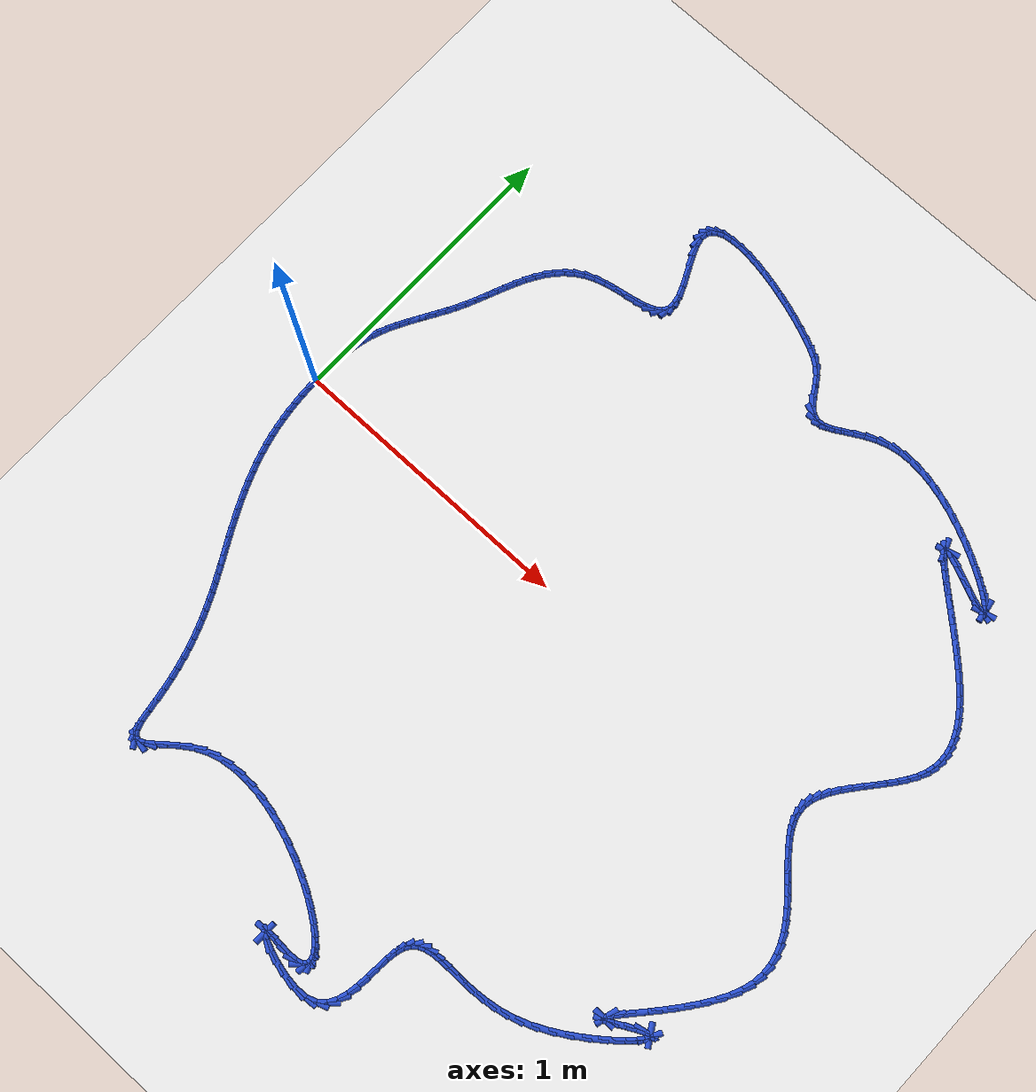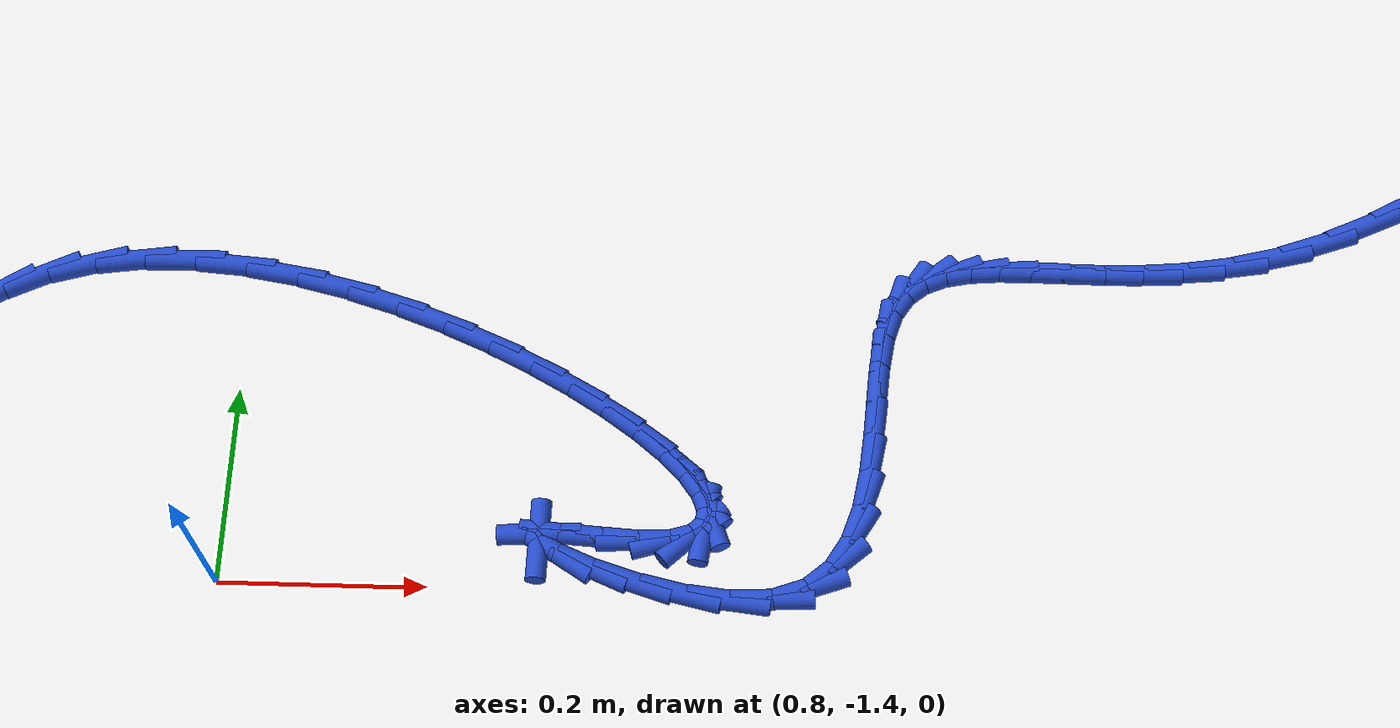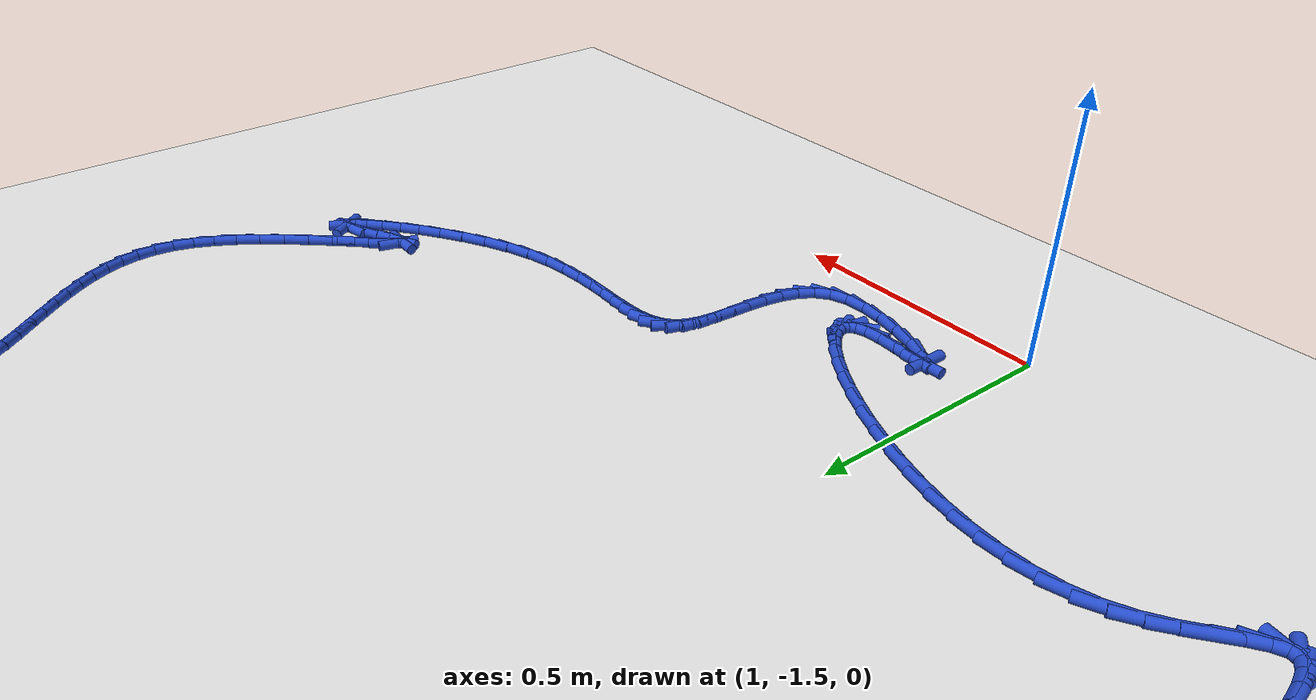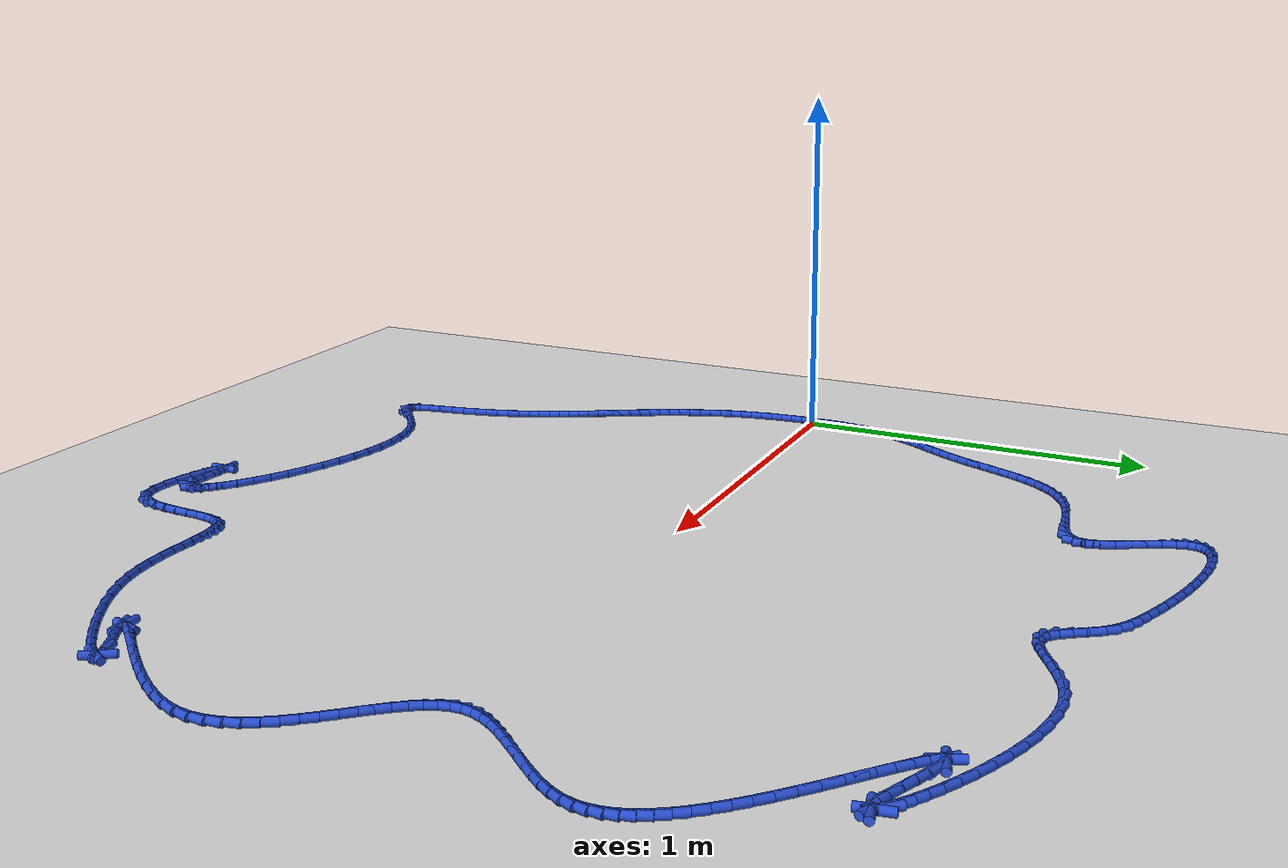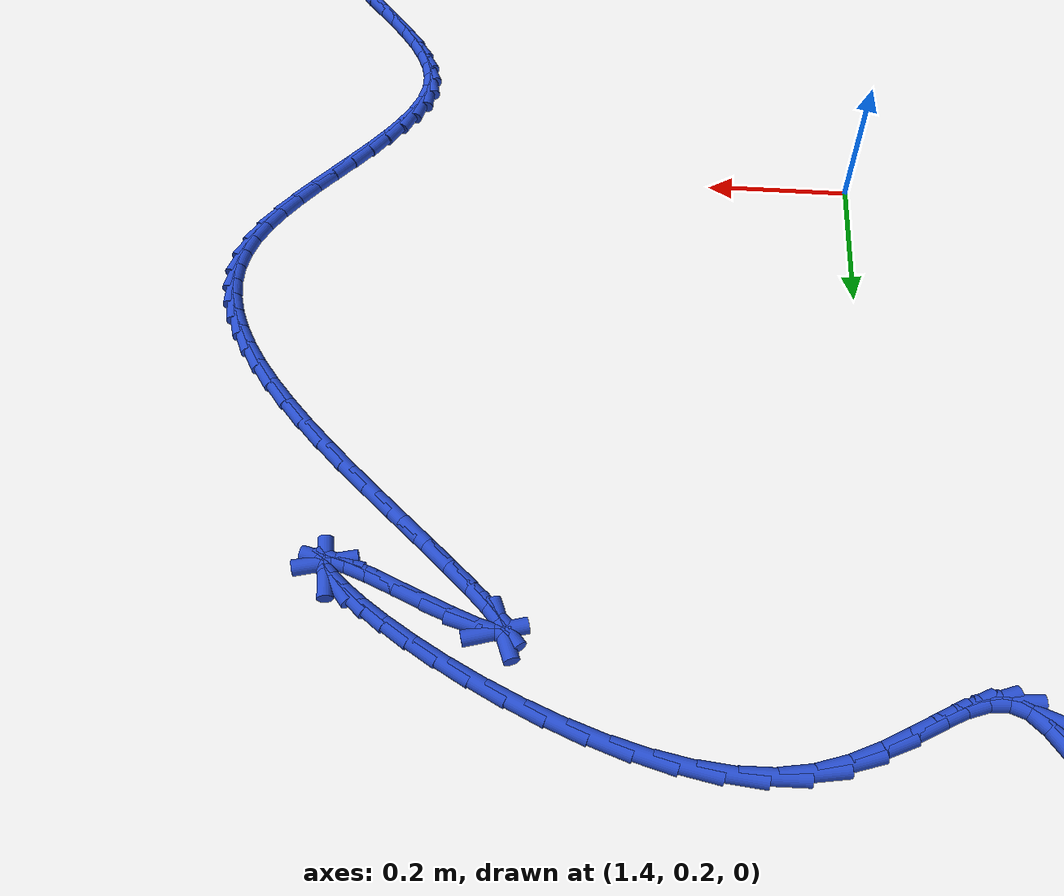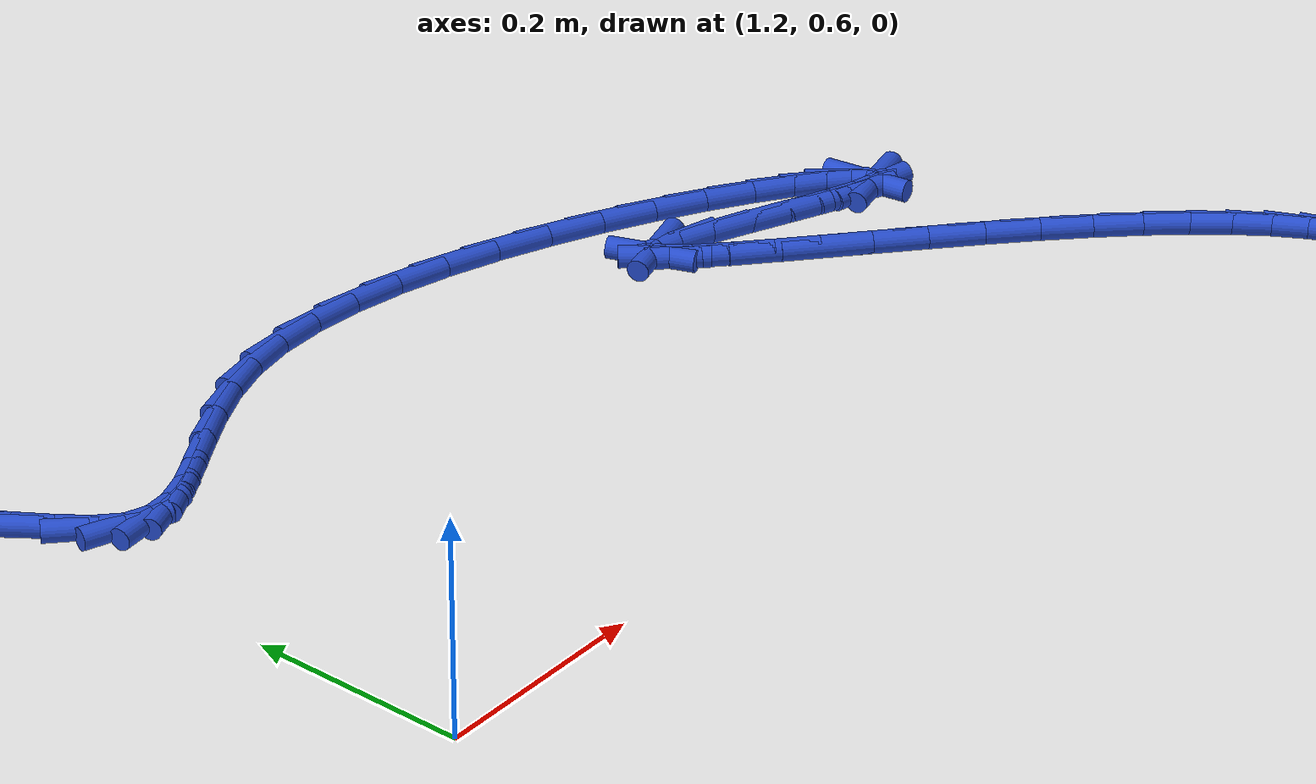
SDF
<sdf version="1.6">
 <world name="default">
  <light name="sun" type="directional">
   <pose>0 0 10 0 -0 0</pose>
   <diffuse>0.8 0.8 0.8 1</diffuse>
   <specular>0.2 0.2 0.2 1</specular>
   <attenuation>
    <range>1000</range>
    <constant>0.9</constant>
    <linear>0.01</linear>
    <quadratic>0.001</quadratic>
   </attenuation>
   <direction>-0.5 0.1 -0.9</direction>
  </light>
  <model name="ground_plane">
   <static>1</static>
   <link name="link">
    <collision name="collision">
     <geometry><plane><normal>0 0 1</normal><size>100 100</size></plane></geometry>
     <surface><friction><ode><mu>100</mu><mu2>50</mu2></ode></friction></surface>
    </collision>
    <visual name="visual">
     <cast_shadows>0</cast_shadows>
     <geometry><plane><normal>0 0 1</normal><size>100 100</size></plane></geometry>
     <material>
      <script><uri>file://media/materials/scripts/gazebo.material</uri><name>Gazebo/WhiteGlow</name></script>
     </material>
    </visual>
   </link>
  </model>
  <gravity>0 0 -9.8</gravity>
  <magnetic_field>6e-06 2.3e-05 -4.2e-05</magnetic_field>
  <atmosphere type="adiabatic"/>
  <physics name="default_physics" default="0" type="ode">
   <max_step_size>0.001</max_step_size>
   <real_time_factor>1</real_time_factor>
   <real_time_update_rate>1000</real_time_update_rate>
  </physics>
  <scene><ambient>0.4 0.4 0.4 1</ambient><background>0.7 0.7 0.7 1</background><shadows>1</shadows></scene>
  <spherical_coordinates>
   <surface_model>EARTH_WGS84</surface_model>
   <latitude_deg>0</latitude_deg>
   <longitude_deg>0</longitude_deg>
   <elevation>0</elevation>
   <heading_deg>0</heading_deg>
  </spherical_coordinates>
  <model name="line">
   <link name="link_0">
    <pose>-9.107298248878237e-18 -6.245004513516506e-17 0.01 0 1.57 -1.5658944839849958</pose>
    <collision name="collision">
     <geometry><cylinder><radius>0.01</radius><length>0.08</length></cylinder></geometry>
    </collision>
    <visual name="visual">
     <material>
      <script><name>Gazebo/Blue</name><uri>file://media/materials/scripts/gazebo.material</uri></script>
     </material>
     <geometry><cylinder><radius>0.01</radius><length>0.08</length></cylinder></geometry>
    </visual>
   </link>
   <link name="link_1">
    <pose>-0.00016155652832458892 0.03295806100365336 0.01 0 1.57 1.5474566577063693</pose>
    <collision name="collision">
     <geometry><cylinder><radius>0.01</radius><length>0.08</length></cylinder></geometry>
    </collision>
    <visual name="visual">
     <material>
      <script><name>Gazebo/Blue</name><uri>file://media/materials/scripts/gazebo.material</uri></script>
     </material>
     <geometry><cylinder><radius>0.01</radius><length>0.08</length></cylinder></geometry>
    </visual>
   </link>
   <link name="link_2">
    <pose>0.0006087739015508442 0.06595726700076039 0.01 0 1.57 1.5124248729891052</pose>
    <collision name="collision">
     <geometry><cylinder><radius>0.01</radius><length>0.08</length></cylinder></geometry>
    </collision>
    <visual name="visual">
     <material>
      <script><name>Gazebo/Blue</name><uri>file://media/materials/scripts/gazebo.material</uri></script>
     </material>
     <geometry><cylinder><radius>0.01</radius><length>0.08</length></cylinder></geometry>
    </visual>
   </link>
   <link name="link_3">
    <pose>0.002529834421990248 0.09883083909902339 0.01 0 1.57 1.4701395982767924</pose>
    <collision name="collision">
     <geometry><cylinder><radius>0.01</radius><length>0.08</length></cylinder></geometry>
    </collision>
    <visual name="visual">
     <material>
      <script><name>Gazebo/Blue</name><uri>file://media/materials/scripts/gazebo.material</uri></script>
     </material>
     <geometry><cylinder><radius>0.01</radius><length>0.08</length></cylinder></geometry>
    </visual>
   </link>
   <link name="link_4">
    <pose>0.005820468165357586 0.13141199840614484 0.01 0 1.57 1.4200571307159806</pose>
    <collision name="collision">
     <geometry><cylinder><radius>0.01</radius><length>0.08</length></cylinder></geometry>
    </collision>
    <visual name="visual">
     <material>
      <script><name>Gazebo/Blue</name><uri>file://media/materials/scripts/gazebo.material</uri></script>
     </material>
     <geometry><cylinder><radius>0.01</radius><length>0.08</length></cylinder></geometry>
    </visual>
   </link>
   <link name="link_5">
    <pose>0.010699518264016817 0.16353396602982717 0.01 0 1.57 1.3616111288394246</pose>
    <collision name="collision">
     <geometry><cylinder><radius>0.01</radius><length>0.08</length></cylinder></geometry>
    </collision>
    <visual name="visual">
     <material>
      <script><name>Gazebo/Blue</name><uri>file://media/materials/scripts/gazebo.material</uri></script>
     </material>
     <geometry><cylinder><radius>0.01</radius><length>0.08</length></cylinder></geometry>
    </visual>
   </link>
   <link name="link_6">
    <pose>0.017385827850331905 0.19502996307777282 0.01 0 1.57 1.294306598906461</pose>
    <collision name="collision">
     <geometry><cylinder><radius>0.01</radius><length>0.08</length></cylinder></geometry>
    </collision>
    <visual name="visual">
     <material>
      <script><name>Gazebo/Blue</name><uri>file://media/materials/scripts/gazebo.material</uri></script>
     </material>
     <geometry><cylinder><radius>0.01</radius><length>0.08</length></cylinder></geometry>
    </visual>
   </link>
   <link name="link_7">
    <pose>0.02609812848399147 0.2257332823142468 0.01 0 1.57 1.2224607399121636</pose>
    <collision name="collision">
     <geometry><cylinder><radius>0.01</radius><length>0.08</length></cylinder></geometry>
    </collision>
    <visual name="visual">
     <material>
      <script><name>Gazebo/Blue</name><uri>file://media/materials/scripts/gazebo.material</uri></script>
     </material>
     <geometry><cylinder><radius>0.01</radius><length>0.08</length></cylinder></geometry>
    </visual>
   </link>
   <link name="link_8">
    <pose>0.036928890658805155 0.2555583065548617 0.01 0 1.57 1.160038678555661</pose>
    <collision name="collision">
     <geometry><cylinder><radius>0.01</radius><length>0.08</length></cylinder></geometry>
    </collision>
    <visual name="visual">
     <material>
      <script><name>Gazebo/Blue</name><uri>file://media/materials/scripts/gazebo.material</uri></script>
     </material>
     <geometry><cylinder><radius>0.01</radius><length>0.08</length></cylinder></geometry>
    </visual>
   </link>
   <link name="link_9">
    <pose>0.04960194979171867 0.2846561712285821 0.01 0 1.57 1.1102378742927024</pose>
    <collision name="collision">
     <geometry><cylinder><radius>0.01</radius><length>0.08</length></cylinder></geometry>
    </collision>
    <visual name="visual">
     <material>
      <script><name>Gazebo/Blue</name><uri>file://media/materials/scripts/gazebo.material</uri></script>
     </material>
     <geometry><cylinder><radius>0.01</radius><length>0.08</length></cylinder></geometry>
    </visual>
   </link>
   <link name="link_10">
    <pose>0.06377422615985905 0.31322098742029647 0.01 0 1.57 1.073295075942822</pose>
    <collision name="collision">
     <geometry><cylinder><radius>0.01</radius><length>0.08</length></cylinder></geometry>
    </collision>
    <visual name="visual">
     <material>
      <script><name>Gazebo/Blue</name><uri>file://media/materials/scripts/gazebo.material</uri></script>
     </material>
     <geometry><cylinder><radius>0.01</radius><length>0.08</length></cylinder></geometry>
    </visual>
   </link>
   <link name="link_11">
    <pose>0.0791026400403533 0.3414468662148935 0.01 0 1.57 1.0490994446726534</pose>
    <collision name="collision">
     <geometry><cylinder><radius>0.01</radius><length>0.08</length></cylinder></geometry>
    </collision>
    <visual name="visual">
     <material>
      <script><name>Gazebo/Blue</name><uri>file://media/materials/scripts/gazebo.material</uri></script>
     </material>
     <geometry><cylinder><radius>0.01</radius><length>0.08</length></cylinder></geometry>
    </visual>
   </link>
   <link name="link_12">
    <pose>0.09524411171032846 0.3695279186972616 0.01 0 1.57 1.0373786063809063</pose>
    <collision name="collision">
     <geometry><cylinder><radius>0.01</radius><length>0.08</length></cylinder></geometry>
    </collision>
    <visual name="visual">
     <material>
      <script><name>Gazebo/Blue</name><uri>file://media/materials/scripts/gazebo.material</uri></script>
     </material>
     <geometry><cylinder><radius>0.01</radius><length>0.08</length></cylinder></geometry>
    </visual>
   </link>
   <link name="link_13">
    <pose>0.11185556144691154 0.39765825595228954 0.01 0 1.57 1.0378185432117668</pose>
    <collision name="collision">
     <geometry><cylinder><radius>0.01</radius><length>0.08</length></cylinder></geometry>
    </collision>
    <visual name="visual">
     <material>
      <script><name>Gazebo/Blue</name><uri>file://media/materials/scripts/gazebo.material</uri></script>
     </material>
     <geometry><cylinder><radius>0.01</radius><length>0.08</length></cylinder></geometry>
    </visual>
   </link>
   <link name="link_14">
    <pose>0.1285939095272296 0.4260319890648658 0.01 0 1.57 1.050118261876973</pose>
    <collision name="collision">
     <geometry><cylinder><radius>0.01</radius><length>0.08</length></cylinder></geometry>
    </collision>
    <visual name="visual">
     <material>
      <script><name>Gazebo/Blue</name><uri>file://media/materials/scripts/gazebo.material</uri></script>
     </material>
     <geometry><cylinder><radius>0.01</radius><length>0.08</length></cylinder></geometry>
    </visual>
   </link>
   <link name="link_15">
    <pose>0.14511607622840958 0.45484322911987884 0.01 0 1.57 1.0739878810053047</pose>
    <collision name="collision">
     <geometry><cylinder><radius>0.01</radius><length>0.08</length></cylinder></geometry>
    </collision>
    <visual name="visual">
     <material>
      <script><name>Gazebo/Blue</name><uri>file://media/materials/scripts/gazebo.material</uri></script>
     </material>
     <geometry><cylinder><radius>0.01</radius><length>0.08</length></cylinder></geometry>
    </visual>
   </link>
   <link name="link_16">
    <pose>0.16107898182757863 0.4842860872022175 0.01 0 1.57 1.108871123853095</pose>
    <collision name="collision">
     <geometry><cylinder><radius>0.01</radius><length>0.08</length></cylinder></geometry>
    </collision>
    <visual name="visual">
     <material>
      <script><name>Gazebo/Blue</name><uri>file://media/materials/scripts/gazebo.material</uri></script>
     </material>
     <geometry><cylinder><radius>0.01</radius><length>0.08</length></cylinder></geometry>
    </visual>
   </link>
   <link name="link_17">
    <pose>0.1761458402041488 0.5145500088563273 0.01 0 1.57 1.1441048032050112</pose>
    <collision name="collision">
     <geometry><cylinder><radius>0.01</radius><length>0.08</length></cylinder></geometry>
    </collision>
    <visual name="visual">
     <material>
      <script><name>Gazebo/Blue</name><uri>file://media/materials/scripts/gazebo.material</uri></script>
     </material>
     <geometry><cylinder><radius>0.01</radius><length>0.08</length></cylinder></geometry>
    </visual>
   </link>
   <link name="link_18">
    <pose>0.1902671025750306 0.5456115063407476 0.01 0 1.57 1.1656597654194376</pose>
    <collision name="collision">
     <geometry><cylinder><radius>0.01</radius><length>0.08</length></cylinder></geometry>
    </collision>
    <visual name="visual">
     <material>
      <script><name>Gazebo/Blue</name><uri>file://media/materials/scripts/gazebo.material</uri></script>
     </material>
     <geometry><cylinder><radius>0.01</radius><length>0.08</length></cylinder></geometry>
    </visual>
   </link>
   <link name="link_19">
    <pose>0.20379303893328274 0.5771507003428037 0.01 0 1.57 1.1729823307309297</pose>
    <collision name="collision">
     <geometry><cylinder><radius>0.01</radius><length>0.08</length></cylinder></geometry>
    </collision>
    <visual name="visual">
     <material>
      <script><name>Gazebo/Blue</name><uri>file://media/materials/scripts/gazebo.material</uri></script>
     </material>
     <geometry><cylinder><radius>0.01</radius><length>0.08</length></cylinder></geometry>
    </visual>
   </link>
   <link name="link_20">
    <pose>0.21710350393702937 0.6088257800001147 0.01 0 1.57 1.1662249180799666</pose>
    <collision name="collision">
     <geometry><cylinder><radius>0.01</radius><length>0.08</length></cylinder></geometry>
    </collision>
    <visual name="visual">
     <material>
      <script><name>Gazebo/Blue</name><uri>file://media/materials/scripts/gazebo.material</uri></script>
     </material>
     <geometry><cylinder><radius>0.01</radius><length>0.08</length></cylinder></geometry>
    </visual>
   </link>
   <link name="link_21">
    <pose>0.23057835224439466 0.6402949344502994 0.01 0 1.57 1.1451369291719409</pose>
    <collision name="collision">
     <geometry><cylinder><radius>0.01</radius><length>0.08</length></cylinder></geometry>
    </collision>
    <visual name="visual">
     <material>
      <script><name>Gazebo/Blue</name><uri>file://media/materials/scripts/gazebo.material</uri></script>
     </material>
     <geometry><cylinder><radius>0.01</radius><length>0.08</length></cylinder></geometry>
    </visual>
   </link>
   <link name="link_22">
    <pose>0.24459743851350257 0.6712163528309769 0.01 0 1.57 1.1090887185943108</pose>
    <collision name="collision">
     <geometry><cylinder><radius>0.01</radius><length>0.08</length></cylinder></geometry>
    </collision>
    <visual name="visual">
     <material>
      <script><name>Gazebo/Blue</name><uri>file://media/materials/scripts/gazebo.material</uri></script>
     </material>
     <geometry><cylinder><radius>0.01</radius><length>0.08</length></cylinder></geometry>
    </visual>
   </link>
   <link name="link_23">
    <pose>0.25954061740247736 0.7012482242797664 0.01 0 1.57 1.05717234348854</pose>
    <collision name="collision">
     <geometry><cylinder><radius>0.01</radius><length>0.08</length></cylinder></geometry>
    </collision>
    <visual name="visual">
     <material>
      <script><name>Gazebo/Blue</name><uri>file://media/materials/scripts/gazebo.material</uri></script>
     </material>
     <geometry><cylinder><radius>0.01</radius><length>0.08</length></cylinder></geometry>
    </visual>
   </link>
   <link name="link_24">
    <pose>0.2757877435694432 0.7300487379342866 0.01 0 1.57 0.9884248001463394</pose>
    <collision name="collision">
     <geometry><cylinder><radius>0.01</radius><length>0.08</length></cylinder></geometry>
    </collision>
    <visual name="visual">
     <material>
      <script><name>Gazebo/Blue</name><uri>file://media/materials/scripts/gazebo.material</uri></script>
     </material>
     <geometry><cylinder><radius>0.01</radius><length>0.08</length></cylinder></geometry>
    </visual>
   </link>
   <link name="link_25">
    <pose>0.293718671672524 0.7572760829321569 0.01 0 1.57 0.9022358878521407</pose>
    <collision name="collision">
     <geometry><cylinder><radius>0.01</radius><length>0.08</length></cylinder></geometry>
    </collision>
    <visual name="visual">
     <material>
      <script><name>Gazebo/Blue</name><uri>file://media/materials/scripts/gazebo.material</uri></script>
     </material>
     <geometry><cylinder><radius>0.01</radius><length>0.08</length></cylinder></geometry>
    </visual>
   </link>
   <link name="link_26">
    <pose>0.31371325636984404 0.7825884484109962 0.01 0 1.57 0.7989701882500563</pose>
    <collision name="collision">
     <geometry><cylinder><radius>0.01</radius><length>0.08</length></cylinder></geometry>
    </collision>
    <visual name="visual">
     <material>
      <script><name>Gazebo/Blue</name><uri>file://media/materials/scripts/gazebo.material</uri></script>
     </material>
     <geometry><cylinder><radius>0.01</radius><length>0.08</length></cylinder></geometry>
    </visual>
   </link>
   <link name="link_27">
    <pose>0.3361513523195273 0.8056440235084233 0.01 0 1.57 0.6806938380511588</pose>
    <collision name="collision">
     <geometry><cylinder><radius>0.01</radius><length>0.08</length></cylinder></geometry>
    </collision>
    <visual name="visual">
     <material>
      <script><name>Gazebo/Blue</name><uri>file://media/materials/scripts/gazebo.material</uri></script>
     </material>
     <geometry><cylinder><radius>0.01</radius><length>0.08</length></cylinder></geometry>
    </visual>
   </link>
   <link name="link_28">
    <pose>0.36141281417969817 0.8261009973620578 0.01 0 1.57 0.5516507551160256</pose>
    <collision name="collision">
     <geometry><cylinder><radius>0.01</radius><length>0.08</length></cylinder></geometry>
    </collision>
    <visual name="visual">
     <material>
      <script><name>Gazebo/Blue</name><uri>file://media/materials/scripts/gazebo.material</uri></script>
     </material>
     <geometry><cylinder><radius>0.01</radius><length>0.08</length></cylinder></geometry>
    </visual>
   </link>
   <link name="link_29">
    <pose>0.38987749660848037 0.8436175591095181 0.01 0 1.57 0.41798695435497035</pose>
    <collision name="collision">
     <geometry><cylinder><radius>0.01</radius><length>0.08</length></cylinder></geometry>
    </collision>
    <visual name="visual">
     <material>
      <script><name>Gazebo/Blue</name><uri>file://media/materials/scripts/gazebo.material</uri></script>
     </material>
     <geometry><cylinder><radius>0.01</radius><length>0.08</length></cylinder></geometry>
    </visual>
   </link>
   <link name="link_30">
    <pose>0.42192525426399846 0.8578518978884235 0.01 0 1.57 0.29323474519452153</pose>
    <collision name="collision">
     <geometry><cylinder><radius>0.01</radius><length>0.08</length></cylinder></geometry>
    </collision>
    <visual name="visual">
     <material>
      <script><name>Gazebo/Blue</name><uri>file://media/materials/scripts/gazebo.material</uri></script>
     </material>
     <geometry><cylinder><radius>0.01</radius><length>0.08</length></cylinder></geometry>
    </visual>
   </link>
   <link name="link_31">
    <pose>0.45767301450054715 0.8686455409579862 0.01 0 1.57 0.21296572190392837</pose>
    <collision name="collision">
     <geometry><cylinder><radius>0.01</radius><length>0.08</length></cylinder></geometry>
    </collision>
    <visual name="visual">
     <material>
      <script><name>Gazebo/Blue</name><uri>file://media/materials/scripts/gazebo.material</uri></script>
     </material>
     <geometry><cylinder><radius>0.01</radius><length>0.08</length></cylinder></geometry>
    </visual>
   </link>
   <link name="link_32">
    <pose>0.49574769273384056 0.8768789947400706 0.01 0 1.57 0.1778053408781745</pose>
    <collision name="collision">
     <geometry><cylinder><radius>0.01</radius><length>0.08</length></cylinder></geometry>
    </collision>
    <visual name="visual">
     <material>
      <script><name>Gazebo/Blue</name><uri>file://media/materials/scripts/gazebo.material</uri></script>
     </material>
     <geometry><cylinder><radius>0.01</radius><length>0.08</length></cylinder></geometry>
    </visual>
   </link>
   <link name="link_33">
    <pose>0.5342519465096038 0.8837983285011534 0.01 0 1.57 0.18293295546383148</pose>
    <collision name="collision">
     <geometry><cylinder><radius>0.01</radius><length>0.08</length></cylinder></geometry>
    </collision>
    <visual name="visual">
     <material>
      <script><name>Gazebo/Blue</name><uri>file://media/materials/scripts/gazebo.material</uri></script>
     </material>
     <geometry><cylinder><radius>0.01</radius><length>0.08</length></cylinder></geometry>
    </visual>
   </link>
   <link name="link_34">
    <pose>0.5712878523724615 0.8906500166373763 0.01 0 1.57 0.23413487884796141</pose>
    <collision name="collision">
     <geometry><cylinder><radius>0.01</radius><length>0.08</length></cylinder></geometry>
    </collision>
    <visual name="visual">
     <material>
      <script><name>Gazebo/Blue</name><uri>file://media/materials/scripts/gazebo.material</uri></script>
     </material>
     <geometry><cylinder><radius>0.01</radius><length>0.08</length></cylinder></geometry>
    </visual>
   </link>
   <link name="link_35">
    <pose>0.6049574868670381 0.8986805335448811 0.01 0 1.57 0.35270078433831425</pose>
    <collision name="collision">
     <geometry><cylinder><radius>0.01</radius><length>0.08</length></cylinder></geometry>
    </collision>
    <visual name="visual">
     <material>
      <script><name>Gazebo/Blue</name><uri>file://media/materials/scripts/gazebo.material</uri></script>
     </material>
     <geometry><cylinder><radius>0.01</radius><length>0.08</length></cylinder></geometry>
    </visual>
   </link>
   <link name="link_36">
    <pose>0.6333629265379582 0.9091363536198094 0.01 0 1.57 0.5868736189940619</pose>
    <collision name="collision">
     <geometry><cylinder><radius>0.01</radius><length>0.08</length></cylinder></geometry>
    </collision>
    <visual name="visual">
     <material>
      <script><name>Gazebo/Blue</name><uri>file://media/materials/scripts/gazebo.material</uri></script>
     </material>
     <geometry><cylinder><radius>0.01</radius><length>0.08</length></cylinder></geometry>
    </visual>
   </link>
   <link name="link_37">
    <pose>0.6546062479298468 0.923263951258303 0.01 0 1.57 1.0016968772270858</pose>
    <collision name="collision">
     <geometry><cylinder><radius>0.01</radius><length>0.08</length></cylinder></geometry>
    </collision>
    <visual name="visual">
     <material>
      <script><name>Gazebo/Blue</name><uri>file://media/materials/scripts/gazebo.material</uri></script>
     </material>
     <geometry><cylinder><radius>0.01</radius><length>0.08</length></cylinder></geometry>
    </visual>
   </link>
   <link name="link_38">
    <pose>0.6667897614419297 0.9423096559597306 0.01 0 1.57 1.4863423343294806</pose>
    <collision name="collision">
     <geometry><cylinder><radius>0.01</radius><length>0.08</length></cylinder></geometry>
    </collision>
    <visual name="visual">
     <material>
      <script><name>Gazebo/Blue</name><uri>file://media/materials/scripts/gazebo.material</uri></script>
     </material>
     <geometry><cylinder><radius>0.01</radius><length>0.08</length></cylinder></geometry>
    </visual>
   </link>
   <link name="link_39">
    <pose>0.668878673742882 0.9669851449939091 0.01 0 1.57 -1.361037192958256</pose>
    <collision name="collision">
     <geometry><cylinder><radius>0.01</radius><length>0.08</length></cylinder></geometry>
    </collision>
    <visual name="visual">
     <material>
      <script><name>Gazebo/Blue</name><uri>file://media/materials/scripts/gazebo.material</uri></script>
     </material>
     <geometry><cylinder><radius>0.01</radius><length>0.08</length></cylinder></geometry>
    </visual>
   </link>
   <link name="link_40">
    <pose>0.66264579945127 0.9962624962103419 0.01 0 1.57 -1.2113510625095167</pose>
    <collision name="collision">
     <geometry><cylinder><radius>0.01</radius><length>0.08</length></cylinder></geometry>
    </collision>
    <visual name="visual">
     <material>
      <script><name>Gazebo/Blue</name><uri>file://media/materials/scripts/gazebo.material</uri></script>
     </material>
     <geometry><cylinder><radius>0.01</radius><length>0.08</length></cylinder></geometry>
    </visual>
   </link>
   <link name="link_41">
    <pose>0.6504340049012347 1.028760582291836 0.01 0 1.57 -1.1383961814823833</pose>
    <collision name="collision">
     <geometry><cylinder><radius>0.01</radius><length>0.08</length></cylinder></geometry>
    </collision>
    <visual name="visual">
     <material>
      <script><name>Gazebo/Blue</name><uri>file://media/materials/scripts/gazebo.material</uri></script>
     </material>
     <geometry><cylinder><radius>0.01</radius><length>0.08</length></cylinder></geometry>
    </visual>
   </link>
   <link name="link_42">
    <pose>0.6345861564269176 1.0630982759211978 0.01 0 1.57 -1.113076028456115</pose>
    <collision name="collision">
     <geometry><cylinder><radius>0.01</radius><length>0.08</length></cylinder></geometry>
    </collision>
    <visual name="visual">
     <material>
      <script><name>Gazebo/Blue</name><uri>file://media/materials/scripts/gazebo.material</uri></script>
     </material>
     <geometry><cylinder><radius>0.01</radius><length>0.08</length></cylinder></geometry>
    </visual>
   </link>
   <link name="link_43">
    <pose>0.6174451203624599 1.0978944497812342 0.01 0 1.57 -1.127313495933282</pose>
    <collision name="collision">
     <geometry><cylinder><radius>0.01</radius><length>0.08</length></cylinder></geometry>
    </collision>
    <visual name="visual">
     <material>
      <script><name>Gazebo/Blue</name><uri>file://media/materials/scripts/gazebo.material</uri></script>
     </material>
     <geometry><cylinder><radius>0.01</radius><length>0.08</length></cylinder></geometry>
    </visual>
   </link>
   <link name="link_44">
    <pose>0.6013537630420026 1.1317679765547524 0.01 0 1.57 -1.1883550900838769</pose>
    <collision name="collision">
     <geometry><cylinder><radius>0.01</radius><length>0.08</length></cylinder></geometry>
    </collision>
    <visual name="visual">
     <material>
      <script><name>Gazebo/Blue</name><uri>file://media/materials/scripts/gazebo.material</uri></script>
     </material>
     <geometry><cylinder><radius>0.01</radius><length>0.08</length></cylinder></geometry>
    </visual>
   </link>
   <link name="link_45">
    <pose>0.5886549507996872 1.1633377289245581 0.01 0 1.57 -1.326081347961942</pose>
    <collision name="collision">
     <geometry><cylinder><radius>0.01</radius><length>0.08</length></cylinder></geometry>
    </collision>
    <visual name="visual">
     <material>
      <script><name>Gazebo/Blue</name><uri>file://media/materials/scripts/gazebo.material</uri></script>
     </material>
     <geometry><cylinder><radius>0.01</radius><length>0.08</length></cylinder></geometry>
    </visual>
   </link>
   <link name="link_46">
    <pose>0.5816915499696549 1.1912225795734592 0.01 0 1.57 1.5312222667075162</pose>
    <collision name="collision">
     <geometry><cylinder><radius>0.01</radius><length>0.08</length></cylinder></geometry>
    </collision>
    <visual name="visual">
     <material>
      <script><name>Gazebo/Blue</name><uri>file://media/materials/scripts/gazebo.material</uri></script>
     </material>
     <geometry><cylinder><radius>0.01</radius><length>0.08</length></cylinder></geometry>
    </visual>
   </link>
   <link name="link_47">
    <pose>0.5825995621508034 1.214155230788296 0.01 0 1.57 1.1026287620602837</pose>
    <collision name="collision">
     <geometry><cylinder><radius>0.01</radius><length>0.08</length></cylinder></geometry>
    </collision>
    <visual name="visual">
     <material>
      <script><name>Gazebo/Blue</name><uri>file://media/materials/scripts/gazebo.material</uri></script>
     </material>
     <geometry><cylinder><radius>0.01</radius><length>0.08</length></cylinder></geometry>
    </visual>
   </link>
   <link name="link_48">
    <pose>0.5915871864608415 1.231929179451142 0.01 0 1.57 0.6749368980002889</pose>
    <collision name="collision">
     <geometry><cylinder><radius>0.01</radius><length>0.08</length></cylinder></geometry>
    </collision>
    <visual name="visual">
     <material>
      <script><name>Gazebo/Blue</name><uri>file://media/materials/scripts/gazebo.material</uri></script>
     </material>
     <geometry><cylinder><radius>0.01</radius><length>0.08</length></cylinder></geometry>
    </visual>
   </link>
   <link name="link_49">
    <pose>0.6078133280040979 1.2449153080575177 0.01 0 1.57 0.3624519466559067</pose>
    <collision name="collision">
     <geometry><cylinder><radius>0.01</radius><length>0.08</length></cylinder></geometry>
    </collision>
    <visual name="visual">
     <material>
      <script><name>Gazebo/Blue</name><uri>file://media/materials/scripts/gazebo.material</uri></script>
     </material>
     <geometry><cylinder><radius>0.01</radius><length>0.08</length></cylinder></geometry>
    </visual>
   </link>
   <link name="link_50">
    <pose>0.6304263777736273 1.2534902846087292 0.01 0 1.57 0.15992822698306933</pose>
    <collision name="collision">
     <geometry><cylinder><radius>0.01</radius><length>0.08</length></cylinder></geometry>
    </collision>
    <visual name="visual">
     <material>
      <script><name>Gazebo/Blue</name><uri>file://media/materials/scripts/gazebo.material</uri></script>
     </material>
     <geometry><cylinder><radius>0.01</radius><length>0.08</length></cylinder></geometry>
    </visual>
   </link>
   <link name="link_51">
    <pose>0.6585747267624839 1.2580307771060848 0.01 0 1.57 0.026878131774821942</pose>
    <collision name="collision">
     <geometry><cylinder><radius>0.01</radius><length>0.08</length></cylinder></geometry>
    </collision>
    <visual name="visual">
     <material>
      <script><name>Gazebo/Blue</name><uri>file://media/materials/scripts/gazebo.material</uri></script>
     </material>
     <geometry><cylinder><radius>0.01</radius><length>0.08</length></cylinder></geometry>
    </visual>
   </link>
   <link name="link_52">
    <pose>0.6914067659637232 1.258913453550892 0.01 0 1.57 -0.06532432712867192</pose>
    <collision name="collision">
     <geometry><cylinder><radius>0.01</radius><length>0.08</length></cylinder></geometry>
    </collision>
    <visual name="visual">
     <material>
      <script><name>Gazebo/Blue</name><uri>file://media/materials/scripts/gazebo.material</uri></script>
     </material>
     <geometry><cylinder><radius>0.01</radius><length>0.08</length></cylinder></geometry>
    </visual>
   </link>
   <link name="link_53">
    <pose>0.7280708863703993 1.2565149819444574 0.01 0 1.57 -0.13297297661138285</pose>
    <collision name="collision">
     <geometry><cylinder><radius>0.01</radius><length>0.08</length></cylinder></geometry>
    </collision>
    <visual name="visual">
     <material>
      <script><name>Gazebo/Blue</name><uri>file://media/materials/scripts/gazebo.material</uri></script>
     </material>
     <geometry><cylinder><radius>0.01</radius><length>0.08</length></cylinder></geometry>
    </visual>
   </link>
   <link name="link_54">
    <pose>0.7677154789755671 1.251212030288089 0.01 0 1.57 -0.18530726575082315</pose>
    <collision name="collision">
     <geometry><cylinder><radius>0.01</radius><length>0.08</length></cylinder></geometry>
    </collision>
    <visual name="visual">
     <material>
      <script><name>Gazebo/Blue</name><uri>file://media/materials/scripts/gazebo.material</uri></script>
     </material>
     <geometry><cylinder><radius>0.01</radius><length>0.08</length></cylinder></geometry>
    </visual>
   </link>
   <link name="link_55">
    <pose>0.8094889347722817 1.2433812665830934 0.01 0 1.57 -0.2278379685912845</pose>
    <collision name="collision">
     <geometry><cylinder><radius>0.01</radius><length>0.08</length></cylinder></geometry>
    </collision>
    <visual name="visual">
     <material>
      <script><name>Gazebo/Blue</name><uri>file://media/materials/scripts/gazebo.material</uri></script>
     </material>
     <geometry><cylinder><radius>0.01</radius><length>0.08</length></cylinder></geometry>
    </visual>
   </link>
   <link name="link_56">
    <pose>0.8525396447535973 1.2333993588307788 0.01 0 1.57 -0.2640927065759335</pose>
    <collision name="collision">
     <geometry><cylinder><radius>0.01</radius><length>0.08</length></cylinder></geometry>
    </collision>
    <visual name="visual">
     <material>
      <script><name>Gazebo/Blue</name><uri>file://media/materials/scripts/gazebo.material</uri></script>
     </material>
     <geometry><cylinder><radius>0.01</radius><length>0.08</length></cylinder></geometry>
    </visual>
   </link>
   <link name="link_57">
    <pose>0.8960159999125691 1.2216429750324518 0.01 0 1.57 -0.29654380360677063</pose>
    <collision name="collision">
     <geometry><cylinder><radius>0.01</radius><length>0.08</length></cylinder></geometry>
    </collision>
    <visual name="visual">
     <material>
      <script><name>Gazebo/Blue</name><uri>file://media/materials/scripts/gazebo.material</uri></script>
     </material>
     <geometry><cylinder><radius>0.01</radius><length>0.08</length></cylinder></geometry>
    </visual>
   </link>
   <link name="link_58">
    <pose>0.9390663912422516 1.2084887831894207 0.01 0 1.57 -0.3271498618571152</pose>
    <collision name="collision">
     <geometry><cylinder><radius>0.01</radius><length>0.08</length></cylinder></geometry>
    </collision>
    <visual name="visual">
     <material>
      <script><name>Gazebo/Blue</name><uri>file://media/materials/scripts/gazebo.material</uri></script>
     </material>
     <geometry><cylinder><radius>0.01</radius><length>0.08</length></cylinder></geometry>
    </visual>
   </link>
   <link name="link_59">
    <pose>0.9808392097356997 1.194313451302992 0.01 0 1.57 -0.35774061045233907</pose>
    <collision name="collision">
     <geometry><cylinder><radius>0.01</radius><length>0.08</length></cylinder></geometry>
    </collision>
    <visual name="visual">
     <material>
      <script><name>Gazebo/Blue</name><uri>file://media/materials/scripts/gazebo.material</uri></script>
     </material>
     <geometry><cylinder><radius>0.01</radius><length>0.08</length></cylinder></geometry>
    </visual>
   </link>
   <link name="link_60">
    <pose>1.0204828463859676 1.1794936473744735 0.01 0 1.57 -0.39040044620142456</pose>
    <collision name="collision">
     <geometry><cylinder><radius>0.01</radius><length>0.08</length></cylinder></geometry>
    </collision>
    <visual name="visual">
     <material>
      <script><name>Gazebo/Blue</name><uri>file://media/materials/scripts/gazebo.material</uri></script>
     </material>
     <geometry><cylinder><radius>0.01</radius><length>0.08</length></cylinder></geometry>
    </visual>
   </link>
   <link name="link_61">
    <pose>1.0571456921861109 1.164406039405172 0.01 0 1.57 -0.4290235555523064</pose>
    <collision name="collision">
     <geometry><cylinder><radius>0.01</radius><length>0.08</length></cylinder></geometry>
    </collision>
    <visual name="visual">
     <material>
      <script><name>Gazebo/Blue</name><uri>file://media/materials/scripts/gazebo.material</uri></script>
     </material>
     <geometry><cylinder><radius>0.01</radius><length>0.08</length></cylinder></geometry>
    </visual>
   </link>
   <link name="link_62">
    <pose>1.0900070629147665 1.1493739428864636 0.01 0 1.57 -0.5007394149446814</pose>
    <collision name="collision">
     <geometry><cylinder><radius>0.01</radius><length>0.08</length></cylinder></geometry>
    </collision>
    <visual name="visual">
     <material>
      <script><name>Gazebo/Blue</name><uri>file://media/materials/scripts/gazebo.material</uri></script>
     </material>
     <geometry><cylinder><radius>0.01</radius><length>0.08</length></cylinder></geometry>
    </visual>
   </link>
   <link name="link_63">
    <pose>1.118926261108187 1.1335475366313033 0.01 0 1.57 -0.6305753564823436</pose>
    <collision name="collision">
     <geometry><cylinder><radius>0.01</radius><length>0.08</length></cylinder></geometry>
    </collision>
    <visual name="visual">
     <material>
      <script><name>Gazebo/Blue</name><uri>file://media/materials/scripts/gazebo.material</uri></script>
     </material>
     <geometry><cylinder><radius>0.01</radius><length>0.08</length></cylinder></geometry>
    </visual>
   </link>
   <link name="link_64">
    <pose>1.1444256375596882 1.1149330856613644 0.01 0 1.57 -0.8028672189630411</pose>
    <collision name="collision">
     <geometry><cylinder><radius>0.01</radius><length>0.08</length></cylinder></geometry>
    </collision>
    <visual name="visual">
     <material>
      <script><name>Gazebo/Blue</name><uri>file://media/materials/scripts/gazebo.material</uri></script>
     </material>
     <geometry><cylinder><radius>0.01</radius><length>0.08</length></cylinder></geometry>
    </visual>
   </link>
   <link name="link_65">
    <pose>1.167055743605833 1.091498185596402 0.01 0 1.57 -0.9478825323363468</pose>
    <collision name="collision">
     <geometry><cylinder><radius>0.01</radius><length>0.08</length></cylinder></geometry>
    </collision>
    <visual name="visual">
     <material>
      <script><name>Gazebo/Blue</name><uri>file://media/materials/scripts/gazebo.material</uri></script>
     </material>
     <geometry><cylinder><radius>0.01</radius><length>0.08</length></cylinder></geometry>
    </visual>
   </link>
   <link name="link_66">
    <pose>1.187503972121403 1.0630313287265598 0.01 0 1.57 -0.9951427723197955</pose>
    <collision name="collision">
     <geometry><cylinder><radius>0.01</radius><length>0.08</length></cylinder></geometry>
    </collision>
    <visual name="visual">
     <material>
      <script><name>Gazebo/Blue</name><uri>file://media/materials/scripts/gazebo.material</uri></script>
     </material>
     <geometry><cylinder><radius>0.01</radius><length>0.08</length></cylinder></geometry>
    </visual>
   </link>
   <link name="link_67">
    <pose>1.2067611078545082 1.033358123989123 0.01 0 1.57 -0.9465445864385512</pose>
    <collision name="collision">
     <geometry><cylinder><radius>0.01</radius><length>0.08</length></cylinder></geometry>
    </collision>
    <visual name="visual">
     <material>
      <script><name>Gazebo/Blue</name><uri>file://media/materials/scripts/gazebo.material</uri></script>
     </material>
     <geometry><cylinder><radius>0.01</radius><length>0.08</length></cylinder></geometry>
    </visual>
   </link>
   <link name="link_68">
    <pose>1.225858690586729 1.0068464915648403 0.01 0 1.57 -0.7600534953009594</pose>
    <collision name="collision">
     <geometry><cylinder><radius>0.01</radius><length>0.08</length></cylinder></geometry>
    </collision>
    <visual name="visual">
     <material>
      <script><name>Gazebo/Blue</name><uri>file://media/materials/scripts/gazebo.material</uri></script>
     </material>
     <geometry><cylinder><radius>0.01</radius><length>0.08</length></cylinder></geometry>
    </visual>
   </link>
   <link name="link_69">
    <pose>1.2458282600996473 0.987864351634463 0.01 0 1.57 -0.3537460817427655</pose>
    <collision name="collision">
     <geometry><cylinder><radius>0.01</radius><length>0.08</length></cylinder></geometry>
    </collision>
    <visual name="visual">
     <material>
      <script><name>Gazebo/Blue</name><uri>file://media/materials/scripts/gazebo.material</uri></script>
     </material>
     <geometry><cylinder><radius>0.01</radius><length>0.08</length></cylinder></geometry>
    </visual>
   </link>
   <link name="link_70">
    <pose>1.2675772241700207 0.9798329037707363 0.01 0 1.57 0.0798149576238006</pose>
    <collision name="collision">
     <geometry><cylinder><radius>0.01</radius><length>0.08</length></cylinder></geometry>
    </collision>
    <visual name="visual">
     <material>
      <script><name>Gazebo/Blue</name><uri>file://media/materials/scripts/gazebo.material</uri></script>
     </material>
     <geometry><cylinder><radius>0.01</radius><length>0.08</length></cylinder></geometry>
    </visual>
   </link>
   <link name="link_71">
    <pose>1.2914318188066443 0.9817409105588127 0.01 0 1.57 0.3502315399643494</pose>
    <collision name="collision">
     <geometry><cylinder><radius>0.01</radius><length>0.08</length></cylinder></geometry>
    </collision>
    <visual name="visual">
     <material>
      <script><name>Gazebo/Blue</name><uri>file://media/materials/scripts/gazebo.material</uri></script>
     </material>
     <geometry><cylinder><radius>0.01</radius><length>0.08</length></cylinder></geometry>
    </visual>
   </link>
   <link name="link_72">
    <pose>1.3175483385461255 0.9912810377867015 0.01 0 1.57 0.48025554968265743</pose>
    <collision name="collision">
     <geometry><cylinder><radius>0.01</radius><length>0.08</length></cylinder></geometry>
    </collision>
    <visual name="visual">
     <material>
      <script><name>Gazebo/Blue</name><uri>file://media/materials/scripts/gazebo.material</uri></script>
     </material>
     <geometry><cylinder><radius>0.01</radius><length>0.08</length></cylinder></geometry>
    </visual>
   </link>
   <link name="link_73">
    <pose>1.3460830569537183 1.0061457912996596 0.01 0 1.57 0.5216917624543608</pose>
    <collision name="collision">
     <geometry><cylinder><radius>0.01</radius><length>0.08</length></cylinder></geometry>
    </collision>
    <visual name="visual">
     <material>
      <script><name>Gazebo/Blue</name><uri>file://media/materials/scripts/gazebo.material</uri></script>
     </material>
     <geometry><cylinder><radius>0.01</radius><length>0.08</length></cylinder></geometry>
    </visual>
   </link>
   <link name="link_74">
    <pose>1.3771922475946734 1.024027676942943 0.01 0 1.57 0.5023793213527683</pose>
    <collision name="collision">
     <geometry><cylinder><radius>0.01</radius><length>0.08</length></cylinder></geometry>
    </collision>
    <visual name="visual">
     <material>
      <script><name>Gazebo/Blue</name><uri>file://media/materials/scripts/gazebo.material</uri></script>
     </material>
     <geometry><cylinder><radius>0.01</radius><length>0.08</length></cylinder></geometry>
    </visual>
   </link>
   <link name="link_75">
    <pose>1.411032184034244 1.042619200561809 0.01 0 1.57 0.43336726780103724</pose>
    <collision name="collision">
     <geometry><cylinder><radius>0.01</radius><length>0.08</length></cylinder></geometry>
    </collision>
    <visual name="visual">
     <material>
      <script><name>Gazebo/Blue</name><uri>file://media/materials/scripts/gazebo.material</uri></script>
     </material>
     <geometry><cylinder><radius>0.01</radius><length>0.08</length></cylinder></geometry>
    </visual>
   </link>
   <link name="link_76">
    <pose>1.4477591398376823 1.059612868001513 0.01 0 1.57 0.3179341001916274</pose>
    <collision name="collision">
     <geometry><cylinder><radius>0.01</radius><length>0.08</length></cylinder></geometry>
    </collision>
    <visual name="visual">
     <material>
      <script><name>Gazebo/Blue</name><uri>file://media/materials/scripts/gazebo.material</uri></script>
     </material>
     <geometry><cylinder><radius>0.01</radius><length>0.08</length></cylinder></geometry>
    </visual>
   </link>
   <link name="link_77">
    <pose>1.4875293885702408 1.0727011851073125 0.01 0 1.57 0.1632786894948163</pose>
    <collision name="collision">
     <geometry><cylinder><radius>0.01</radius><length>0.08</length></cylinder></geometry>
    </collision>
    <visual name="visual">
     <material>
      <script><name>Gazebo/Blue</name><uri>file://media/materials/scripts/gazebo.material</uri></script>
     </material>
     <geometry><cylinder><radius>0.01</radius><length>0.08</length></cylinder></geometry>
    </visual>
   </link>
   <link name="link_78">
    <pose>1.5304401018681406 1.0797705247820657 0.01 0 1.57 0.017157606060357683</pose>
    <collision name="collision">
     <geometry><cylinder><radius>0.01</radius><length>0.08</length></cylinder></geometry>
    </collision>
    <visual name="visual">
     <material>
      <script><name>Gazebo/Blue</name><uri>file://media/materials/scripts/gazebo.material</uri></script>
     </material>
     <geometry><cylinder><radius>0.01</radius><length>0.08</length></cylinder></geometry>
    </visual>
   </link>
   <link name="link_79">
    <pose>1.5760258408252927 1.080552743692002 0.01 0 1.57 -0.09973049262688012</pose>
    <collision name="collision">
     <geometry><cylinder><radius>0.01</radius><length>0.08</length></cylinder></geometry>
    </collision>
    <visual name="visual">
     <material>
      <script><name>Gazebo/Blue</name><uri>file://media/materials/scripts/gazebo.material</uri></script>
     </material>
     <geometry><cylinder><radius>0.01</radius><length>0.08</length></cylinder></geometry>
    </visual>
   </link>
   <link name="link_80">
    <pose>1.6235096949201488 1.0758013924921106 0.01 0 1.57 -0.1934394493840396</pose>
    <collision name="collision">
     <geometry><cylinder><radius>0.01</radius><length>0.08</length></cylinder></geometry>
    </collision>
    <visual name="visual">
     <material>
      <script><name>Gazebo/Blue</name><uri>file://media/materials/scripts/gazebo.material</uri></script>
     </material>
     <geometry><cylinder><radius>0.01</radius><length>0.08</length></cylinder></geometry>
    </visual>
   </link>
   <link name="link_81">
    <pose>1.6721114529713472 1.0662808487125188 0.01 0 1.57 -0.2696387362456919</pose>
    <collision name="collision">
     <geometry><cylinder><radius>0.01</radius><length>0.08</length></cylinder></geometry>
    </collision>
    <visual name="visual">
     <material>
      <script><name>Gazebo/Blue</name><uri>file://media/materials/scripts/gazebo.material</uri></script>
     </material>
     <geometry><cylinder><radius>0.01</radius><length>0.08</length></cylinder></geometry>
    </visual>
   </link>
   <link name="link_82">
    <pose>1.7210509037975263 1.052755489883352 0.01 0 1.57 -0.3328464531535941</pose>
    <collision name="collision">
     <geometry><cylinder><radius>0.01</radius><length>0.08</length></cylinder></geometry>
    </collision>
    <visual name="visual">
     <material>
      <script><name>Gazebo/Blue</name><uri>file://media/materials/scripts/gazebo.material</uri></script>
     </material>
     <geometry><cylinder><radius>0.01</radius><length>0.08</length></cylinder></geometry>
    </visual>
   </link>
   <link name="link_83">
    <pose>1.7695478362173225 1.0359896935347366 0.01 0 1.57 -0.38654904492334824</pose>
    <collision name="collision">
     <geometry><cylinder><radius>0.01</radius><length>0.08</length></cylinder></geometry>
    </collision>
    <visual name="visual">
     <material>
      <script><name>Gazebo/Blue</name><uri>file://media/materials/scripts/gazebo.material</uri></script>
     </material>
     <geometry><cylinder><radius>0.01</radius><length>0.08</length></cylinder></geometry>
    </visual>
   </link>
   <link name="link_84">
    <pose>1.816822039049374 1.0167478371967995 0.01 0 1.57 -0.43348363728287115</pose>
    <collision name="collision">
     <geometry><cylinder><radius>0.01</radius><length>0.08</length></cylinder></geometry>
    </collision>
    <visual name="visual">
     <material>
      <script><name>Gazebo/Blue</name><uri>file://media/materials/scripts/gazebo.material</uri></script>
     </material>
     <geometry><cylinder><radius>0.01</radius><length>0.08</length></cylinder></geometry>
    </visual>
   </link>
   <link name="link_85">
    <pose>1.862093301112319 0.9957942983996669 0.01 0 1.57 -0.47593753497241514</pose>
    <collision name="collision">
     <geometry><cylinder><radius>0.01</radius><length>0.08</length></cylinder></geometry>
    </collision>
    <visual name="visual">
     <material>
      <script><name>Gazebo/Blue</name><uri>file://media/materials/scripts/gazebo.material</uri></script>
     </material>
     <geometry><cylinder><radius>0.01</radius><length>0.08</length></cylinder></geometry>
    </visual>
   </link>
   <link name="link_86">
    <pose>1.9045814112247956 0.9738934546734649 0.01 0 1.57 -0.5160625197754991</pose>
    <collision name="collision">
     <geometry><cylinder><radius>0.01</radius><length>0.08</length></cylinder></geometry>
    </collision>
    <visual name="visual">
     <material>
      <script><name>Gazebo/Blue</name><uri>file://media/materials/scripts/gazebo.material</uri></script>
     </material>
     <geometry><cylinder><radius>0.01</radius><length>0.08</length></cylinder></geometry>
    </visual>
   </link>
   <link name="link_87">
    <pose>1.943506158205442 0.9518096835483196 0.01 0 1.57 -0.5562896226902618</pose>
    <collision name="collision">
     <geometry><cylinder><radius>0.01</radius><length>0.08</length></cylinder></geometry>
    </collision>
    <visual name="visual">
     <material>
      <script><name>Gazebo/Blue</name><uri>file://media/materials/scripts/gazebo.material</uri></script>
     </material>
     <geometry><cylinder><radius>0.01</radius><length>0.08</length></cylinder></geometry>
    </visual>
   </link>
   <link name="link_88">
    <pose>1.9780873308728955 0.9303073625543583 0.01 0 1.57 -0.6000834849711446</pose>
    <collision name="collision">
     <geometry><cylinder><radius>0.01</radius><length>0.08</length></cylinder></geometry>
    </collision>
    <visual name="visual">
     <material>
      <script><name>Gazebo/Blue</name><uri>file://media/materials/scripts/gazebo.material</uri></script>
     </material>
     <geometry><cylinder><radius>0.01</radius><length>0.08</length></cylinder></geometry>
    </visual>
   </link>
   <link name="link_89">
    <pose>2.0075447180457937 0.9101508692217067 0.01 0 1.57 -0.6537801948910908</pose>
    <collision name="collision">
     <geometry><cylinder><radius>0.01</radius><length>0.08</length></cylinder></geometry>
    </collision>
    <visual name="visual">
     <material>
      <script><name>Gazebo/Blue</name><uri>file://media/materials/scripts/gazebo.material</uri></script>
     </material>
     <geometry><cylinder><radius>0.01</radius><length>0.08</length></cylinder></geometry>
    </visual>
   </link>
   <link name="link_90">
    <pose>2.0310981085427753 0.8921045810804913 0.01 0 1.57 -0.7324691755194301</pose>
    <collision name="collision">
     <geometry><cylinder><radius>0.01</radius><length>0.08</length></cylinder></geometry>
    </collision>
    <visual name="visual">
     <material>
      <script><name>Gazebo/Blue</name><uri>file://media/materials/scripts/gazebo.material</uri></script>
     </material>
     <geometry><cylinder><radius>0.01</radius><length>0.08</length></cylinder></geometry>
    </visual>
   </link>
   <link name="link_91">
    <pose>2.047967291182478 0.8769328756608381 0.01 0 1.57 -0.8866852633292297</pose>
    <collision name="collision">
     <geometry><cylinder><radius>0.01</radius><length>0.08</length></cylinder></geometry>
    </collision>
    <visual name="visual">
     <material>
      <script><name>Gazebo/Blue</name><uri>file://media/materials/scripts/gazebo.material</uri></script>
     </material>
     <geometry><cylinder><radius>0.01</radius><length>0.08</length></cylinder></geometry>
    </visual>
   </link>
   <link name="link_92">
    <pose>2.0573720547835395 0.8654001304928742 0.01 0 1.57 -1.4094851415332712</pose>
    <collision name="collision">
     <geometry><cylinder><radius>0.01</radius><length>0.08</length></cylinder></geometry>
    </collision>
    <visual name="visual">
     <material>
      <script><name>Gazebo/Blue</name><uri>file://media/materials/scripts/gazebo.material</uri></script>
     </material>
     <geometry><cylinder><radius>0.01</radius><length>0.08</length></cylinder></geometry>
    </visual>
   </link>
   <link name="link_93">
    <pose>2.0585321881645973 0.8582707231067255 0.01 0 1.57 0.24444187556262414</pose>
    <collision name="collision">
     <geometry><cylinder><radius>0.01</radius><length>0.08</length></cylinder></geometry>
    </collision>
    <visual name="visual">
     <material>
      <script><name>Gazebo/Blue</name><uri>file://media/materials/scripts/gazebo.material</uri></script>
     </material>
     <geometry><cylinder><radius>0.01</radius><length>0.08</length></cylinder></geometry>
    </visual>
   </link>
   <link name="link_94">
    <pose>2.0506674801442903 0.8563090310325188 0.01 0 1.57 -0.22102917914361375</pose>
    <collision name="collision">
     <geometry><cylinder><radius>0.01</radius><length>0.08</length></cylinder></geometry>
    </collision>
    <visual name="visual">
     <material>
      <script><name>Gazebo/Blue</name><uri>file://media/materials/scripts/gazebo.material</uri></script>
     </material>
     <geometry><cylinder><radius>0.01</radius><length>0.08</length></cylinder></geometry>
    </visual>
   </link>
   <link name="link_95">
    <pose>2.0329977195453632 0.8602794317975283 0.01 0 1.57 -0.3529485117211044</pose>
    <collision name="collision">
     <geometry><cylinder><radius>0.01</radius><length>0.08</length></cylinder></geometry>
    </collision>
    <visual name="visual">
     <material>
      <script><name>Gazebo/Blue</name><uri>file://media/materials/scripts/gazebo.material</uri></script>
     </material>
     <geometry><cylinder><radius>0.01</radius><length>0.08</length></cylinder></geometry>
    </visual>
   </link>
   <link name="link_96">
    <pose>2.005536131628062 0.8703955528686829 0.01 0 1.57 -0.39685641079395584</pose>
    <collision name="collision">
     <geometry><cylinder><radius>0.01</radius><length>0.08</length></cylinder></geometry>
    </collision>
    <visual name="visual">
     <material>
      <script><name>Gazebo/Blue</name><uri>file://media/materials/scripts/gazebo.material</uri></script>
     </material>
     <geometry><cylinder><radius>0.01</radius><length>0.08</length></cylinder></geometry>
    </visual>
   </link>
   <link name="link_97">
    <pose>1.9714532305381616 0.8846794447168798 0.01 0 1.57 -0.4090068537105748</pose>
    <collision name="collision">
     <geometry><cylinder><radius>0.01</radius><length>0.08</length></cylinder></geometry>
    </collision>
    <visual name="visual">
     <material>
      <script><name>Gazebo/Blue</name><uri>file://media/materials/scripts/gazebo.material</uri></script>
     </material>
     <geometry><cylinder><radius>0.01</radius><length>0.08</length></cylinder></geometry>
    </visual>
   </link>
   <link name="link_98">
    <pose>1.9347047597378095 0.9006081045826113 0.01 0 1.57 -0.4014083073037634</pose>
    <collision name="collision">
     <geometry><cylinder><radius>0.01</radius><length>0.08</length></cylinder></geometry>
    </collision>
    <visual name="visual">
     <material>
      <script><name>Gazebo/Blue</name><uri>file://media/materials/scripts/gazebo.material</uri></script>
     </material>
     <geometry><cylinder><radius>0.01</radius><length>0.08</length></cylinder></geometry>
    </visual>
   </link>
   <link name="link_99">
    <pose>1.8992464626891585 0.915658529706371 0.01 0 1.57 -0.3680109381897119</pose>
    <collision name="collision">
     <geometry><cylinder><radius>0.01</radius><length>0.08</length></cylinder></geometry>
    </collision>
    <visual name="visual">
     <material>
      <script><name>Gazebo/Blue</name><uri>file://media/materials/scripts/gazebo.material</uri></script>
     </material>
     <geometry><cylinder><radius>0.01</radius><length>0.08</length></cylinder></geometry>
    </visual>
   </link>
   <link name="link_100">
    <pose>1.8690340828543561 0.927307717328651 0.01 0 1.57 -0.2660195151744341</pose>
    <collision name="collision">
     <geometry><cylinder><radius>0.01</radius><length>0.08</length></cylinder></geometry>
    </collision>
    <visual name="visual">
     <material>
      <script><name>Gazebo/Blue</name><uri>file://media/materials/scripts/gazebo.material</uri></script>
     </material>
     <geometry><cylinder><radius>0.01</radius><length>0.08</length></cylinder></geometry>
    </visual>
   </link>
   <link name="link_101">
    <pose>1.8480233636955532 0.9330326646899436 0.01 0 1.57 0.2801031239207087</pose>
    <collision name="collision">
     <geometry><cylinder><radius>0.01</radius><length>0.08</length></cylinder></geometry>
    </collision>
    <visual name="visual">
     <material>
      <script><name>Gazebo/Blue</name><uri>file://media/materials/scripts/gazebo.material</uri></script>
     </material>
     <geometry><cylinder><radius>0.01</radius><length>0.08</length></cylinder></geometry>
    </visual>
   </link>
   <link name="link_102">
    <pose>1.8396658897334848 0.9306285037520513 0.01 0 1.57 -1.2015607068183103</pose>
    <collision name="collision">
     <geometry><cylinder><radius>0.01</radius><length>0.08</length></cylinder></geometry>
    </collision>
    <visual name="visual">
     <material>
      <script><name>Gazebo/Blue</name><uri>file://media/materials/scripts/gazebo.material</uri></script>
     </material>
     <geometry><cylinder><radius>0.01</radius><length>0.08</length></cylinder></geometry>
    </visual>
   </link>
   <link name="link_103">
    <pose>1.8436849034186529 0.9202430274493812 0.01 0 1.57 -0.8711445451062044</pose>
    <collision name="collision">
     <geometry><cylinder><radius>0.01</radius><length>0.08</length></cylinder></geometry>
    </collision>
    <visual name="visual">
     <material>
      <script><name>Gazebo/Blue</name><uri>file://media/materials/scripts/gazebo.material</uri></script>
     </material>
     <geometry><cylinder><radius>0.01</radius><length>0.08</length></cylinder></geometry>
    </visual>
   </link>
   <link name="link_104">
    <pose>1.8581316958076495 0.9030790646326948 0.01 0 1.57 -0.7813825399751269</pose>
    <collision name="collision">
     <geometry><cylinder><radius>0.01</radius><length>0.08</length></cylinder></geometry>
    </collision>
    <visual name="visual">
     <material>
      <script><name>Gazebo/Blue</name><uri>file://media/materials/scripts/gazebo.material</uri></script>
     </material>
     <geometry><cylinder><radius>0.01</radius><length>0.08</length></cylinder></geometry>
    </visual>
   </link>
   <link name="link_105">
    <pose>1.8810496521423157 0.880344432885405 0.01 0 1.57 -0.744115724558868</pose>
    <collision name="collision">
     <geometry><cylinder><radius>0.01</radius><length>0.08</length></cylinder></geometry>
    </collision>
    <visual name="visual">
     <material>
      <script><name>Gazebo/Blue</name><uri>file://media/materials/scripts/gazebo.material</uri></script>
     </material>
     <geometry><cylinder><radius>0.01</radius><length>0.08</length></cylinder></geometry>
    </visual>
   </link>
   <link name="link_106">
    <pose>1.9104821576644944 0.8532469497909241 0.01 0 1.57 -0.7272795196205392</pose>
    <collision name="collision">
     <geometry><cylinder><radius>0.01</radius><length>0.08</length></cylinder></geometry>
    </collision>
    <visual name="visual">
     <material>
      <script><name>Gazebo/Blue</name><uri>file://media/materials/scripts/gazebo.material</uri></script>
     </material>
     <geometry><cylinder><radius>0.01</radius><length>0.08</length></cylinder></geometry>
    </visual>
   </link>
   <link name="link_107">
    <pose>1.944472597616027 0.8229944329326642 0.01 0 1.57 -0.721639211436359</pose>
    <collision name="collision">
     <geometry><cylinder><radius>0.01</radius><length>0.08</length></cylinder></geometry>
    </collision>
    <visual name="visual">
     <material>
      <script><name>Gazebo/Blue</name><uri>file://media/materials/scripts/gazebo.material</uri></script>
     </material>
     <geometry><cylinder><radius>0.01</radius><length>0.08</length></cylinder></geometry>
    </visual>
   </link>
   <link name="link_108">
    <pose>1.9810643572387545 0.790794699894038 0.01 0 1.57 -0.7242376804115852</pose>
    <collision name="collision">
     <geometry><cylinder><radius>0.01</radius><length>0.08</length></cylinder></geometry>
    </collision>
    <visual name="visual">
     <material>
      <script><name>Gazebo/Blue</name><uri>file://media/materials/scripts/gazebo.material</uri></script>
     </material>
     <geometry><cylinder><radius>0.01</radius><length>0.08</length></cylinder></geometry>
    </visual>
   </link>
   <link name="link_109">
    <pose>2.0183008217745195 0.7578555682584567 0.01 0 1.57 -0.7347921937396783</pose>
    <collision name="collision">
     <geometry><cylinder><radius>0.01</radius><length>0.08</length></cylinder></geometry>
    </collision>
    <visual name="visual">
     <material>
      <script><name>Gazebo/Blue</name><uri>file://media/materials/scripts/gazebo.material</uri></script>
     </material>
     <geometry><cylinder><radius>0.01</radius><length>0.08</length></cylinder></geometry>
    </visual>
   </link>
   <link name="link_110">
    <pose>2.0542823744322067 0.7253431798769426 0.01 0 1.57 -0.7523948803820598</pose>
    <collision name="collision">
     <geometry><cylinder><radius>0.01</radius><length>0.08</length></cylinder></geometry>
    </collision>
    <visual name="visual">
     <material>
      <script><name>Gazebo/Blue</name><uri>file://media/materials/scripts/gazebo.material</uri></script>
     </material>
     <geometry><cylinder><radius>0.01</radius><length>0.08</length></cylinder></geometry>
    </visual>
   </link>
   <link name="link_111">
    <pose>2.0880405292414888 0.6937428530392217 0.01 0 1.57 -0.7762595078056281</pose>
    <collision name="collision">
     <geometry><cylinder><radius>0.01</radius><length>0.08</length></cylinder></geometry>
    </collision>
    <visual name="visual">
     <material>
      <script><name>Gazebo/Blue</name><uri>file://media/materials/scripts/gazebo.material</uri></script>
     </material>
     <geometry><cylinder><radius>0.01</radius><length>0.08</length></cylinder></geometry>
    </visual>
   </link>
   <link name="link_112">
    <pose>2.1193658544161895 0.6629849013446656 0.01 0 1.57 -0.8074746978622448</pose>
    <collision name="collision">
     <geometry><cylinder><radius>0.01</radius><length>0.08</length></cylinder></geometry>
    </collision>
    <visual name="visual">
     <material>
      <script><name>Gazebo/Blue</name><uri>file://media/materials/scripts/gazebo.material</uri></script>
     </material>
     <geometry><cylinder><radius>0.01</radius><length>0.08</length></cylinder></geometry>
    </visual>
   </link>
   <link name="link_113">
    <pose>2.148071049773217 0.6329834562230834 0.01 0 1.57 -0.847478896991998</pose>
    <collision name="collision">
     <geometry><cylinder><radius>0.01</radius><length>0.08</length></cylinder></geometry>
    </collision>
    <visual name="visual">
     <material>
      <script><name>Gazebo/Blue</name><uri>file://media/materials/scripts/gazebo.material</uri></script>
     </material>
     <geometry><cylinder><radius>0.01</radius><length>0.08</length></cylinder></geometry>
    </visual>
   </link>
   <link name="link_114">
    <pose>2.1739688151294763 0.6036526491042846 0.01 0 1.57 -0.8980481168767065</pose>
    <collision name="collision">
     <geometry><cylinder><radius>0.01</radius><length>0.08</length></cylinder></geometry>
    </collision>
    <visual name="visual">
     <material>
      <script><name>Gazebo/Blue</name><uri>file://media/materials/scripts/gazebo.material</uri></script>
     </material>
     <geometry><cylinder><radius>0.01</radius><length>0.08</length></cylinder></geometry>
    </visual>
   </link>
   <link name="link_115">
    <pose>2.1968718503018767 0.5749066114180786 0.01 0 1.57 -0.9613067160228799</pose>
    <collision name="collision">
     <geometry><cylinder><radius>0.01</radius><length>0.08</length></cylinder></geometry>
    </collision>
    <visual name="visual">
     <material>
      <script><name>Gazebo/Blue</name><uri>file://media/materials/scripts/gazebo.material</uri></script>
     </material>
     <geometry><cylinder><radius>0.01</radius><length>0.08</length></cylinder></geometry>
    </visual>
   </link>
   <link name="link_116">
    <pose>2.216592855107324 0.5466594745942738 0.01 0 1.57 -1.0396417348257783</pose>
    <collision name="collision">
     <geometry><cylinder><radius>0.01</radius><length>0.08</length></cylinder></geometry>
    </collision>
    <visual name="visual">
     <material>
      <script><name>Gazebo/Blue</name><uri>file://media/materials/scripts/gazebo.material</uri></script>
     </material>
     <geometry><cylinder><radius>0.01</radius><length>0.08</length></cylinder></geometry>
    </visual>
   </link>
   <link name="link_117">
    <pose>2.232944529362725 0.5188253700626787 0.01 0 1.57 -1.135409649760142</pose>
    <collision name="collision">
     <geometry><cylinder><radius>0.01</radius><length>0.08</length></cylinder></geometry>
    </collision>
    <visual name="visual">
     <material>
      <script><name>Gazebo/Blue</name><uri>file://media/materials/scripts/gazebo.material</uri></script>
     </material>
     <geometry><cylinder><radius>0.01</radius><length>0.08</length></cylinder></geometry>
    </visual>
   </link>
   <link name="link_118">
    <pose>2.245739572884987 0.4913184292531038 0.01 0 1.57 -1.250281988067868</pose>
    <collision name="collision">
     <geometry><cylinder><radius>0.01</radius><length>0.08</length></cylinder></geometry>
    </collision>
    <visual name="visual">
     <material>
      <script><name>Gazebo/Blue</name><uri>file://media/materials/scripts/gazebo.material</uri></script>
     </material>
     <geometry><cylinder><radius>0.01</radius><length>0.08</length></cylinder></geometry>
    </visual>
   </link>
   <link name="link_119">
    <pose>2.2547906854910176 0.46405278359535745 0.01 0 1.57 -1.3841403913518013</pose>
    <collision name="collision">
     <geometry><cylinder><radius>0.01</radius><length>0.08</length></cylinder></geometry>
    </collision>
    <visual name="visual">
     <material>
      <script><name>Gazebo/Blue</name><uri>file://media/materials/scripts/gazebo.material</uri></script>
     </material>
     <geometry><cylinder><radius>0.01</radius><length>0.08</length></cylinder></geometry>
    </visual>
   </link>
   <link name="link_120">
    <pose>2.2599105669977226 0.43694256451924857 0.01 0 1.57 -1.53378196254658</pose>
    <collision name="collision">
     <geometry><cylinder><radius>0.01</radius><length>0.08</length></cylinder></geometry>
    </collision>
    <visual name="visual">
     <material>
      <script><name>Gazebo/Blue</name><uri>file://media/materials/scripts/gazebo.material</uri></script>
     </material>
     <geometry><cylinder><radius>0.01</radius><length>0.08</length></cylinder></geometry>
    </visual>
   </link>
   <link name="link_121">
    <pose>2.260911917222011 0.40990190345458655 0.01 0 1.57 1.449267685183993</pose>
    <collision name="collision">
     <geometry><cylinder><radius>0.01</radius><length>0.08</length></cylinder></geometry>
    </collision>
    <visual name="visual">
     <material>
      <script><name>Gazebo/Blue</name><uri>file://media/materials/scripts/gazebo.material</uri></script>
     </material>
     <geometry><cylinder><radius>0.01</radius><length>0.08</length></cylinder></geometry>
    </visual>
   </link>
   <link name="link_122">
    <pose>2.2576074359807876 0.38284493183117974 0.01 0 1.57 1.2912084975322835</pose>
    <collision name="collision">
     <geometry><cylinder><radius>0.01</radius><length>0.08</length></cylinder></geometry>
    </collision>
    <visual name="visual">
     <material>
      <script><name>Gazebo/Blue</name><uri>file://media/materials/scripts/gazebo.material</uri></script>
     </material>
     <geometry><cylinder><radius>0.01</radius><length>0.08</length></cylinder></geometry>
    </visual>
   </link>
   <link name="link_123">
    <pose>2.2498098230909602 0.35568578107883797 0.01 0 1.57 1.1450297978765434</pose>
    <collision name="collision">
     <geometry><cylinder><radius>0.01</radius><length>0.08</length></cylinder></geometry>
    </collision>
    <visual name="visual">
     <material>
      <script><name>Gazebo/Blue</name><uri>file://media/materials/scripts/gazebo.material</uri></script>
     </material>
     <geometry><cylinder><radius>0.01</radius><length>0.08</length></cylinder></geometry>
    </visual>
   </link>
   <link name="link_124">
    <pose>2.2374120009756524 0.32834811747883474 0.01 0 1.57 1.0327837691851314</pose>
    <collision name="collision">
     <geometry><cylinder><radius>0.01</radius><length>0.08</length></cylinder></geometry>
    </collision>
    <visual name="visual">
     <material>
      <script><name>Gazebo/Blue</name><uri>file://media/materials/scripts/gazebo.material</uri></script>
     </material>
     <geometry><cylinder><radius>0.01</radius><length>0.08</length></cylinder></geometry>
    </visual>
   </link>
   <link name="link_125">
    <pose>2.2209955284341003 0.300837455134012 0.01 0 1.57 0.9562562717982085</pose>
    <collision name="collision">
     <geometry><cylinder><radius>0.01</radius><length>0.08</length></cylinder></geometry>
    </collision>
    <visual name="visual">
     <material>
      <script><name>Gazebo/Blue</name><uri>file://media/materials/scripts/gazebo.material</uri></script>
     </material>
     <geometry><cylinder><radius>0.01</radius><length>0.08</length></cylinder></geometry>
    </visual>
   </link>
   <link name="link_126">
    <pose>2.201492511306774 0.2732009723878433 0.01 0 1.57 0.9075374635228005</pose>
    <collision name="collision">
     <geometry><cylinder><radius>0.01</radius><length>0.08</length></cylinder></geometry>
    </collision>
    <visual name="visual">
     <material>
      <script><name>Gazebo/Blue</name><uri>file://media/materials/scripts/gazebo.material</uri></script>
     </material>
     <geometry><cylinder><radius>0.01</radius><length>0.08</length></cylinder></geometry>
    </visual>
   </link>
   <link name="link_127">
    <pose>2.1798378344572997 0.2454861778843791 0.01 0 1.57 0.8813967219815108</pose>
    <collision name="collision">
     <geometry><cylinder><radius>0.01</radius><length>0.08</length></cylinder></geometry>
    </collision>
    <visual name="visual">
     <material>
      <script><name>Gazebo/Blue</name><uri>file://media/materials/scripts/gazebo.material</uri></script>
     </material>
     <geometry><cylinder><radius>0.01</radius><length>0.08</length></cylinder></geometry>
    </visual>
   </link>
   <link name="link_128">
    <pose>2.1569663827493026 0.2177405802676685 0.01 0 1.57 0.875081267297095</pose>
    <collision name="collision">
     <geometry><cylinder><radius>0.01</radius><length>0.08</length></cylinder></geometry>
    </collision>
    <visual name="visual">
     <material>
      <script><name>Gazebo/Blue</name><uri>file://media/materials/scripts/gazebo.material</uri></script>
     </material>
     <geometry><cylinder><radius>0.01</radius><length>0.08</length></cylinder></geometry>
    </visual>
   </link>
   <link name="link_129">
    <pose>2.1338130410464076 0.19001168818176084 0.01 0 1.57 0.8879836258896833</pose>
    <collision name="collision">
     <geometry><cylinder><radius>0.01</radius><length>0.08</length></cylinder></geometry>
    </collision>
    <visual name="visual">
     <material>
      <script><name>Gazebo/Blue</name><uri>file://media/materials/scripts/gazebo.material</uri></script>
     </material>
     <geometry><cylinder><radius>0.01</radius><length>0.08</length></cylinder></geometry>
    </visual>
   </link>
   <link name="link_130">
    <pose>2.1113126942122404 0.16234701027070583 0.01 0 1.57 0.9215652570599303</pose>
    <collision name="collision">
     <geometry><cylinder><radius>0.01</radius><length>0.08</length></cylinder></geometry>
    </collision>
    <visual name="visual">
     <material>
      <script><name>Gazebo/Blue</name><uri>file://media/materials/scripts/gazebo.material</uri></script>
     </material>
     <geometry><cylinder><radius>0.01</radius><length>0.08</length></cylinder></geometry>
    </visual>
   </link>
   <link name="link_131">
    <pose>2.090400227110426 0.1347940551785524 0.01 0 1.57 0.9795854422959629</pose>
    <collision name="collision">
     <geometry><cylinder><radius>0.01</radius><length>0.08</length></cylinder></geometry>
    </collision>
    <visual name="visual">
     <material>
      <script><name>Gazebo/Blue</name><uri>file://media/materials/scripts/gazebo.material</uri></script>
     </material>
     <geometry><cylinder><radius>0.01</radius><length>0.08</length></cylinder></geometry>
    </visual>
   </link>
   <link name="link_132">
    <pose>2.0720105246045892 0.10740033154935096 0.01 0 1.57 1.0685403507830098</pose>
    <collision name="collision">
     <geometry><cylinder><radius>0.01</radius><length>0.08</length></cylinder></geometry>
    </collision>
    <visual name="visual">
     <material>
      <script><name>Gazebo/Blue</name><uri>file://media/materials/scripts/gazebo.material</uri></script>
     </material>
     <geometry><cylinder><radius>0.01</radius><length>0.08</length></cylinder></geometry>
    </visual>
   </link>
   <link name="link_133">
    <pose>2.0570784715583565 0.08021334802715055 0.01 0 1.57 1.197788560871915</pose>
    <collision name="collision">
     <geometry><cylinder><radius>0.01</radius><length>0.08</length></cylinder></geometry>
    </collision>
    <visual name="visual">
     <material>
      <script><name>Gazebo/Blue</name><uri>file://media/materials/scripts/gazebo.material</uri></script>
     </material>
     <geometry><cylinder><radius>0.01</radius><length>0.08</length></cylinder></geometry>
    </visual>
   </link>
   <link name="link_134">
    <pose>2.0465389528353524 0.05328061325600064 0.01 0 1.57 1.377523690177215</pose>
    <collision name="collision">
     <geometry><cylinder><radius>0.01</radius><length>0.08</length></cylinder></geometry>
    </collision>
    <visual name="visual">
     <material>
      <script><name>Gazebo/Blue</name><uri>file://media/materials/scripts/gazebo.material</uri></script>
     </material>
     <geometry><cylinder><radius>0.01</radius><length>0.08</length></cylinder></geometry>
    </visual>
   </link>
   <link name="link_135">
    <pose>2.0413268532992026 0.026649635879950354 0.01 0 1.57 -1.5395846699006217</pose>
    <collision name="collision">
     <geometry><cylinder><radius>0.01</radius><length>0.08</length></cylinder></geometry>
    </collision>
    <visual name="visual">
     <material>
      <script><name>Gazebo/Blue</name><uri>file://media/materials/scripts/gazebo.material</uri></script>
     </material>
     <geometry><cylinder><radius>0.01</radius><length>0.08</length></cylinder></geometry>
    </visual>
   </link>
   <link name="link_136">
    <pose>2.0421481240867276 0.00034523019350169207 0.01 0 1.57 -1.3293215959806652</pose>
    <collision name="collision">
     <geometry><cylinder><radius>0.01</radius><length>0.08</length></cylinder></geometry>
    </collision>
    <visual name="visual">
     <material>
      <script><name>Gazebo/Blue</name><uri>file://media/materials/scripts/gazebo.material</uri></script>
     </material>
     <geometry><cylinder><radius>0.01</radius><length>0.08</length></cylinder></geometry>
    </visual>
   </link>
   <link name="link_137">
    <pose>2.048567698679254 -0.025720899332705407 0.01 0 1.57 -1.1624576376299667</pose>
    <collision name="collision">
     <geometry><cylinder><radius>0.01</radius><length>0.08</length></cylinder></geometry>
    </collision>
    <visual name="visual">
     <material>
      <script><name>Gazebo/Blue</name><uri>file://media/materials/scripts/gazebo.material</uri></script>
     </material>
     <geometry><cylinder><radius>0.01</radius><length>0.08</length></cylinder></geometry>
    </visual>
   </link>
   <link name="link_138">
    <pose>2.0597957309310257 -0.0516722177636948 0.01 0 1.57 -1.0397607232825208</pose>
    <collision name="collision">
     <geometry><cylinder><radius>0.01</radius><length>0.08</length></cylinder></geometry>
    </collision>
    <visual name="visual">
     <material>
      <script><name>Gazebo/Blue</name><uri>file://media/materials/scripts/gazebo.material</uri></script>
     </material>
     <geometry><cylinder><radius>0.01</radius><length>0.08</length></cylinder></geometry>
    </visual>
   </link>
   <link name="link_139">
    <pose>2.0750422624456326 -0.07763220129197099 0.01 0 1.57 -0.9546742133846565</pose>
    <collision name="collision">
     <geometry><cylinder><radius>0.01</radius><length>0.08</length></cylinder></geometry>
    </collision>
    <visual name="visual">
     <material>
      <script><name>Gazebo/Blue</name><uri>file://media/materials/scripts/gazebo.material</uri></script>
     </material>
     <geometry><cylinder><radius>0.01</radius><length>0.08</length></cylinder></geometry>
    </visual>
   </link>
   <link name="link_140">
    <pose>2.0935173348266654 -0.10372432611003896 0.01 0 1.57 -0.8998748665494425</pose>
    <collision name="collision">
     <geometry><cylinder><radius>0.01</radius><length>0.08</length></cylinder></geometry>
    </collision>
    <visual name="visual">
     <material>
      <script><name>Gazebo/Blue</name><uri>file://media/materials/scripts/gazebo.material</uri></script>
     </material>
     <geometry><cylinder><radius>0.01</radius><length>0.08</length></cylinder></geometry>
    </visual>
   </link>
   <link name="link_141">
    <pose>2.114430989677713 -0.13007206841040236 0.01 0 1.57 -0.8696903864607244</pose>
    <collision name="collision">
     <geometry><cylinder><radius>0.01</radius><length>0.08</length></cylinder></geometry>
    </collision>
    <visual name="visual">
     <material>
      <script><name>Gazebo/Blue</name><uri>file://media/materials/scripts/gazebo.material</uri></script>
     </material>
     <geometry><cylinder><radius>0.01</radius><length>0.08</length></cylinder></geometry>
    </visual>
   </link>
   <link name="link_142">
    <pose>2.1369932686023643 -0.15679890438556612 0.01 0 1.57 -0.8604481508920307</pose>
    <collision name="collision">
     <geometry><cylinder><radius>0.01</radius><length>0.08</length></cylinder></geometry>
    </collision>
    <visual name="visual">
     <material>
      <script><name>Gazebo/Blue</name><uri>file://media/materials/scripts/gazebo.material</uri></script>
     </material>
     <geometry><cylinder><radius>0.01</radius><length>0.08</length></cylinder></geometry>
    </visual>
   </link>
   <link name="link_143">
    <pose>2.1604142132042092 -0.18402831022803476 0.01 0 1.57 -0.8702226887666695</pose>
    <collision name="collision">
     <geometry><cylinder><radius>0.01</radius><length>0.08</length></cylinder></geometry>
    </collision>
    <visual name="visual">
     <material>
      <script><name>Gazebo/Blue</name><uri>file://media/materials/scripts/gazebo.material</uri></script>
     </material>
     <geometry><cylinder><radius>0.01</radius><length>0.08</length></cylinder></geometry>
    </visual>
   </link>
   <link name="link_144">
    <pose>2.183903865086838 -0.21188376213031285 0.01 0 1.57 -0.8985239679841446</pose>
    <collision name="collision">
     <geometry><cylinder><radius>0.01</radius><length>0.08</length></cylinder></geometry>
    </collision>
    <visual name="visual">
     <material>
      <script><name>Gazebo/Blue</name><uri>file://media/materials/scripts/gazebo.material</uri></script>
     </material>
     <geometry><cylinder><radius>0.01</radius><length>0.08</length></cylinder></geometry>
    </visual>
   </link>
   <link name="link_145">
    <pose>2.2066722658538396 -0.24048873628490486 0.01 0 1.57 -0.9460352512099913</pose>
    <collision name="collision">
     <geometry><cylinder><radius>0.01</radius><length>0.08</length></cylinder></geometry>
    </collision>
    <visual name="visual">
     <material>
      <script><name>Gazebo/Blue</name><uri>file://media/materials/scripts/gazebo.material</uri></script>
     </material>
     <geometry><cylinder><radius>0.01</radius><length>0.08</length></cylinder></geometry>
    </visual>
   </link>
   <link name="link_146">
    <pose>2.227929457108804 -0.26996670888431623 0.01 0 1.57 -1.0143355238114373</pose>
    <collision name="collision">
     <geometry><cylinder><radius>0.01</radius><length>0.08</length></cylinder></geometry>
    </collision>
    <visual name="visual">
     <material>
      <script><name>Gazebo/Blue</name><uri>file://media/materials/scripts/gazebo.material</uri></script>
     </material>
     <geometry><cylinder><radius>0.01</radius><length>0.08</length></cylinder></geometry>
    </visual>
   </link>
   <link name="link_147">
    <pose>2.24688548045532 -0.30044115612104966 0.01 0 1.57 -1.1054360098998903</pose>
    <collision name="collision">
     <geometry><cylinder><radius>0.01</radius><length>0.08</length></cylinder></geometry>
    </collision>
    <visual name="visual">
     <material>
      <script><name>Gazebo/Blue</name><uri>file://media/materials/scripts/gazebo.material</uri></script>
     </material>
     <geometry><cylinder><radius>0.01</radius><length>0.08</length></cylinder></geometry>
    </visual>
   </link>
   <link name="link_148">
    <pose>2.262750377496978 -0.3320355541876106 0.01 0 1.57 -1.2208750515340183</pose>
    <collision name="collision">
     <geometry><cylinder><radius>0.01</radius><length>0.08</length></cylinder></geometry>
    </collision>
    <visual name="visual">
     <material>
      <script><name>Gazebo/Blue</name><uri>file://media/materials/scripts/gazebo.material</uri></script>
     </material>
     <geometry><cylinder><radius>0.01</radius><length>0.08</length></cylinder></geometry>
    </visual>
   </link>
   <link name="link_149">
    <pose>2.2747341898373667 -0.3648733792765035 0.01 0 1.57 -1.3601730682101274</pose>
    <collision name="collision">
     <geometry><cylinder><radius>0.01</radius><length>0.08</length></cylinder></geometry>
    </collision>
    <visual name="visual">
     <material>
      <script><name>Gazebo/Blue</name><uri>file://media/materials/scripts/gazebo.material</uri></script>
     </material>
     <geometry><cylinder><radius>0.01</radius><length>0.08</length></cylinder></geometry>
    </visual>
   </link>
   <link name="link_150">
    <pose>2.282046959080077 -0.399078107580233 0.01 0 1.57 -1.5189654359963876</pose>
    <collision name="collision">
     <geometry><cylinder><radius>0.01</radius><length>0.08</length></cylinder></geometry>
    </collision>
    <visual name="visual">
     <material>
      <script><name>Gazebo/Blue</name><uri>file://media/materials/scripts/gazebo.material</uri></script>
     </material>
     <geometry><cylinder><radius>0.01</radius><length>0.08</length></cylinder></geometry>
    </visual>
   </link>
   <link name="link_151">
    <pose>2.283898726828697 -0.4347732152913033 0.01 0 1.57 1.4534257991829027</pose>
    <collision name="collision">
     <geometry><cylinder><radius>0.01</radius><length>0.08</length></cylinder></geometry>
    </collision>
    <visual name="visual">
     <material>
      <script><name>Gazebo/Blue</name><uri>file://media/materials/scripts/gazebo.material</uri></script>
     </material>
     <geometry><cylinder><radius>0.01</radius><length>0.08</length></cylinder></geometry>
    </visual>
   </link>
   <link name="link_152">
    <pose>2.2794995346868174 -0.47208217860221946 0.01 0 1.57 1.285906423637031</pose>
    <collision name="collision">
     <geometry><cylinder><radius>0.01</radius><length>0.08</length></cylinder></geometry>
    </collision>
    <visual name="visual">
     <material>
      <script><name>Gazebo/Blue</name><uri>file://media/materials/scripts/gazebo.material</uri></script>
     </material>
     <geometry><cylinder><radius>0.01</radius><length>0.08</length></cylinder></geometry>
    </visual>
   </link>
   <link name="link_153">
    <pose>2.268065312016221 -0.5111260101620371 0.01 0 1.57 1.1430301836455485</pose>
    <collision name="collision">
     <geometry><cylinder><radius>0.01</radius><length>0.08</length></cylinder></geometry>
    </collision>
    <visual name="visual">
     <material>
      <script><name>Gazebo/Blue</name><uri>file://media/materials/scripts/gazebo.material</uri></script>
     </material>
     <geometry><cylinder><radius>0.01</radius><length>0.08</length></cylinder></geometry>
    </visual>
   </link>
   <link name="link_154">
    <pose>2.249561243911078 -0.551712220605988 0.01 0 1.57 1.042167589555276</pose>
    <collision name="collision">
     <geometry><cylinder><radius>0.01</radius><length>0.08</length></cylinder></geometry>
    </collision>
    <visual name="visual">
     <material>
      <script><name>Gazebo/Blue</name><uri>file://media/materials/scripts/gazebo.material</uri></script>
     </material>
     <geometry><cylinder><radius>0.01</radius><length>0.08</length></cylinder></geometry>
    </visual>
   </link>
   <link name="link_155">
    <pose>2.2254279275797213 -0.5930309817235416 0.01 0 1.57 0.9710591510638292</pose>
    <collision name="collision">
     <geometry><cylinder><radius>0.01</radius><length>0.08</length></cylinder></geometry>
    </collision>
    <visual name="visual">
     <material>
      <script><name>Gazebo/Blue</name><uri>file://media/materials/scripts/gazebo.material</uri></script>
     </material>
     <geometry><cylinder><radius>0.01</radius><length>0.08</length></cylinder></geometry>
    </visual>
   </link>
   <link name="link_156">
    <pose>2.197278335852723 -0.6342003402574431 0.01 0 1.57 0.9201680870034685</pose>
    <collision name="collision">
     <geometry><cylinder><radius>0.01</radius><length>0.08</length></cylinder></geometry>
    </collision>
    <visual name="visual">
     <material>
      <script><name>Gazebo/Blue</name><uri>file://media/materials/scripts/gazebo.material</uri></script>
     </material>
     <geometry><cylinder><radius>0.01</radius><length>0.08</length></cylinder></geometry>
    </visual>
   </link>
   <link name="link_157">
    <pose>2.166725441560648 -0.6743383429504414 0.01 0 1.57 0.8839947068048503</pose>
    <collision name="collision">
     <geometry><cylinder><radius>0.01</radius><length>0.08</length></cylinder></geometry>
    </collision>
    <visual name="visual">
     <material>
      <script><name>Gazebo/Blue</name><uri>file://media/materials/scripts/gazebo.material</uri></script>
     </material>
     <geometry><cylinder><radius>0.01</radius><length>0.08</length></cylinder></geometry>
    </visual>
   </link>
   <link name="link_158">
    <pose>2.1353822175340653 -0.7125630365452842 0.01 0 1.57 0.8596940541034102</pose>
    <collision name="collision">
     <geometry><cylinder><radius>0.01</radius><length>0.08</length></cylinder></geometry>
    </collision>
    <visual name="visual">
     <material>
      <script><name>Gazebo/Blue</name><uri>file://media/materials/scripts/gazebo.material</uri></script>
     </material>
     <geometry><cylinder><radius>0.01</radius><length>0.08</length></cylinder></geometry>
    </visual>
   </link>
   <link name="link_159">
    <pose>2.104861636603543 -0.7479924677847194 0.01 0 1.57 0.8466087579717633</pose>
    <collision name="collision">
     <geometry><cylinder><radius>0.01</radius><length>0.08</length></cylinder></geometry>
    </collision>
    <visual name="visual">
     <material>
      <script><name>Gazebo/Blue</name><uri>file://media/materials/scripts/gazebo.material</uri></script>
     </material>
     <geometry><cylinder><radius>0.01</radius><length>0.08</length></cylinder></geometry>
    </visual>
   </link>
   <link name="link_160">
    <pose>2.076776671599648 -0.7797446834114944 0.01 0 1.57 0.8469386669329796</pose>
    <collision name="collision">
     <geometry><cylinder><radius>0.01</radius><length>0.08</length></cylinder></geometry>
    </collision>
    <visual name="visual">
     <material>
      <script><name>Gazebo/Blue</name><uri>file://media/materials/scripts/gazebo.material</uri></script>
     </material>
     <geometry><cylinder><radius>0.01</radius><length>0.08</length></cylinder></geometry>
    </visual>
   </link>
   <link name="link_161">
    <pose>2.0527402953529488 -0.8069377301683573 0.01 0 1.57 0.8693613831802628</pose>
    <collision name="collision">
     <geometry><cylinder><radius>0.01</radius><length>0.08</length></cylinder></geometry>
    </collision>
    <visual name="visual">
     <material>
      <script><name>Gazebo/Blue</name><uri>file://media/materials/scripts/gazebo.material</uri></script>
     </material>
     <geometry><cylinder><radius>0.01</radius><length>0.08</length></cylinder></geometry>
    </visual>
   </link>
   <link name="link_162">
    <pose>2.034365480694013 -0.8286896547980557 0.01 0 1.57 0.947135820128232</pose>
    <collision name="collision">
     <geometry><cylinder><radius>0.01</radius><length>0.08</length></cylinder></geometry>
    </collision>
    <visual name="visual">
     <material>
      <script><name>Gazebo/Blue</name><uri>file://media/materials/scripts/gazebo.material</uri></script>
     </material>
     <geometry><cylinder><radius>0.01</radius><length>0.08</length></cylinder></geometry>
    </visual>
   </link>
   <link name="link_163">
    <pose>2.0232652004534075 -0.844118504043337 0.01 0 1.57 1.3079526859081898</pose>
    <collision name="collision">
     <geometry><cylinder><radius>0.01</radius><length>0.08</length></cylinder></geometry>
    </collision>
    <visual name="visual">
     <material>
      <script><name>Gazebo/Blue</name><uri>file://media/materials/scripts/gazebo.material</uri></script>
     </material>
     <geometry><cylinder><radius>0.01</radius><length>0.08</length></cylinder></geometry>
    </visual>
   </link>
   <link name="link_164">
    <pose>2.0210524274617008 -0.8523423246469496 0.01 0 1.57 -0.016509544863523285</pose>
    <collision name="collision">
     <geometry><cylinder><radius>0.01</radius><length>0.08</length></cylinder></geometry>
    </collision>
    <visual name="visual">
     <material>
      <script><name>Gazebo/Blue</name><uri>file://media/materials/scripts/gazebo.material</uri></script>
     </material>
     <geometry><cylinder><radius>0.01</radius><length>0.08</length></cylinder></geometry>
    </visual>
   </link>
   <link name="link_165">
    <pose>2.029340134549462 -0.8524791633516404 0.01 0 1.57 0.40733411551284104</pose>
    <collision name="collision">
     <geometry><cylinder><radius>0.01</radius><length>0.08</length></cylinder></geometry>
    </collision>
    <visual name="visual">
     <material>
      <script><name>Gazebo/Blue</name><uri>file://media/materials/scripts/gazebo.material</uri></script>
     </material>
     <geometry><cylinder><radius>0.01</radius><length>0.08</length></cylinder></geometry>
    </visual>
   </link>
   <link name="link_166">
    <pose>2.049639689196283 -0.8437206082154858 0.01 0 1.57 0.4816849867467591</pose>
    <collision name="collision">
     <geometry><cylinder><radius>0.01</radius><length>0.08</length></cylinder></geometry>
    </collision>
    <visual name="visual">
     <material>
      <script><name>Gazebo/Blue</name><uri>file://media/materials/scripts/gazebo.material</uri></script>
     </material>
     <geometry><cylinder><radius>0.01</radius><length>0.08</length></cylinder></geometry>
    </visual>
   </link>
   <link name="link_167">
    <pose>2.0795758605444554 -0.8280713427796028 0.01 0 1.57 0.48369346340710695</pose>
    <collision name="collision">
     <geometry><cylinder><radius>0.01</radius><length>0.08</length></cylinder></geometry>
    </collision>
    <visual name="visual">
     <material>
      <script><name>Gazebo/Blue</name><uri>file://media/materials/scripts/gazebo.material</uri></script>
     </material>
     <geometry><cylinder><radius>0.01</radius><length>0.08</length></cylinder></geometry>
    </visual>
   </link>
   <link name="link_168">
    <pose>2.111760912364609 -0.811164070513077 0.01 0 1.57 0.4312601188456096</pose>
    <collision name="collision">
     <geometry><cylinder><radius>0.01</radius><length>0.08</length></cylinder></geometry>
    </collision>
    <visual name="visual">
     <material>
      <script><name>Gazebo/Blue</name><uri>file://media/materials/scripts/gazebo.material</uri></script>
     </material>
     <geometry><cylinder><radius>0.01</radius><length>0.08</length></cylinder></geometry>
    </visual>
   </link>
   <link name="link_169">
    <pose>2.138475787100938 -0.7988712991790559 0.01 0 1.57 0.20401162582891663</pose>
    <collision name="collision">
     <geometry><cylinder><radius>0.01</radius><length>0.08</length></cylinder></geometry>
    </collision>
    <visual name="visual">
     <material>
      <script><name>Gazebo/Blue</name><uri>file://media/materials/scripts/gazebo.material</uri></script>
     </material>
     <geometry><cylinder><radius>0.01</radius><length>0.08</length></cylinder></geometry>
    </visual>
   </link>
   <link name="link_170">
    <pose>2.1536334715701053 -0.7957353269610675 0.01 0 1.57 -1.0256027756318968</pose>
    <collision name="collision">
     <geometry><cylinder><radius>0.01</radius><length>0.08</length></cylinder></geometry>
    </collision>
    <visual name="visual">
     <material>
      <script><name>Gazebo/Blue</name><uri>file://media/materials/scripts/gazebo.material</uri></script>
     </material>
     <geometry><cylinder><radius>0.01</radius><length>0.08</length></cylinder></geometry>
    </visual>
   </link>
   <link name="link_171">
    <pose>2.1570981858108222 -0.8014478563259785 0.01 0 1.57 1.0810781060333436</pose>
    <collision name="collision">
     <geometry><cylinder><radius>0.01</radius><length>0.08</length></cylinder></geometry>
    </collision>
    <visual name="visual">
     <material>
      <script><name>Gazebo/Blue</name><uri>file://media/materials/scripts/gazebo.material</uri></script>
     </material>
     <geometry><cylinder><radius>0.01</radius><length>0.08</length></cylinder></geometry>
    </visual>
   </link>
   <link name="link_172">
    <pose>2.1500902645162663 -0.8145952786750572 0.01 0 1.57 0.8673079819084527</pose>
    <collision name="collision">
     <geometry><cylinder><radius>0.01</radius><length>0.08</length></cylinder></geometry>
    </collision>
    <visual name="visual">
     <material>
      <script><name>Gazebo/Blue</name><uri>file://media/materials/scripts/gazebo.material</uri></script>
     </material>
     <geometry><cylinder><radius>0.01</radius><length>0.08</length></cylinder></geometry>
    </visual>
   </link>
   <link name="link_173">
    <pose>2.1338300423796155 -0.8337639854095719 0.01 0 1.57 0.774667951132959</pose>
    <collision name="collision">
     <geometry><cylinder><radius>0.01</radius><length>0.08</length></cylinder></geometry>
    </collision>
    <visual name="visual">
     <material>
      <script><name>Gazebo/Blue</name><uri>file://media/materials/scripts/gazebo.material</uri></script>
     </material>
     <geometry><cylinder><radius>0.01</radius><length>0.08</length></cylinder></geometry>
    </visual>
   </link>
   <link name="link_174">
    <pose>2.1095378540940506 -0.8575403679307897 0.01 0 1.57 0.7143441198098993</pose>
    <collision name="collision">
     <geometry><cylinder><radius>0.01</radius><length>0.08</length></cylinder></geometry>
    </collision>
    <visual name="visual">
     <material>
      <script><name>Gazebo/Blue</name><uri>file://media/materials/scripts/gazebo.material</uri></script>
     </material>
     <geometry><cylinder><radius>0.01</radius><length>0.08</length></cylinder></geometry>
    </visual>
   </link>
   <link name="link_175">
    <pose>2.0784340343527496 -0.884510817639979 0.01 0 1.57 0.6646034830400148</pose>
    <collision name="collision">
     <geometry><cylinder><radius>0.01</radius><length>0.08</length></cylinder></geometry>
    </collision>
    <visual name="visual">
     <material>
      <script><name>Gazebo/Blue</name><uri>file://media/materials/scripts/gazebo.material</uri></script>
     </material>
     <geometry><cylinder><radius>0.01</radius><length>0.08</length></cylinder></geometry>
    </visual>
   </link>
   <link name="link_176">
    <pose>2.041738917848892 -0.913261725938408 0.01 0 1.57 0.6167716563879292</pose>
    <collision name="collision">
     <geometry><cylinder><radius>0.01</radius><length>0.08</length></cylinder></geometry>
    </collision>
    <visual name="visual">
     <material>
      <script><name>Gazebo/Blue</name><uri>file://media/materials/scripts/gazebo.material</uri></script>
     </material>
     <geometry><cylinder><radius>0.01</radius><length>0.08</length></cylinder></geometry>
    </visual>
   </link>
   <link name="link_177">
    <pose>2.000672839275657 -0.9423794842273451 0.01 0 1.57 0.565651511263607</pose>
    <collision name="collision">
     <geometry><cylinder><radius>0.01</radius><length>0.08</length></cylinder></geometry>
    </collision>
    <visual name="visual">
     <material>
      <script><name>Gazebo/Blue</name><uri>file://media/materials/scripts/gazebo.material</uri></script>
     </material>
     <geometry><cylinder><radius>0.01</radius><length>0.08</length></cylinder></geometry>
    </visual>
   </link>
   <link name="link_178">
    <pose>1.9564561333262231 -0.970450483908058 0.01 0 1.57 0.5066581080242607</pose>
    <collision name="collision">
     <geometry><cylinder><radius>0.01</radius><length>0.08</length></cylinder></geometry>
    </collision>
    <visual name="visual">
     <material>
      <script><name>Gazebo/Blue</name><uri>file://media/materials/scripts/gazebo.material</uri></script>
     </material>
     <geometry><cylinder><radius>0.01</radius><length>0.08</length></cylinder></geometry>
    </visual>
   </link>
   <link name="link_179">
    <pose>1.9103091346937693 -0.9960611163818149 0.01 0 1.57 0.4343478405028655</pose>
    <collision name="collision">
     <geometry><cylinder><radius>0.01</radius><length>0.08</length></cylinder></geometry>
    </collision>
    <visual name="visual">
     <material>
      <script><name>Gazebo/Blue</name><uri>file://media/materials/scripts/gazebo.material</uri></script>
     </material>
     <geometry><cylinder><radius>0.01</radius><length>0.08</length></cylinder></geometry>
    </visual>
   </link>
   <link name="link_180">
    <pose>1.8634521780714746 -1.017797773049884 0.01 0 1.57 0.3419640729251842</pose>
    <collision name="collision">
     <geometry><cylinder><radius>0.01</radius><length>0.08</length></cylinder></geometry>
    </collision>
    <visual name="visual">
     <material>
      <script><name>Gazebo/Blue</name><uri>file://media/materials/scripts/gazebo.material</uri></script>
     </material>
     <geometry><cylinder><radius>0.01</radius><length>0.08</length></cylinder></geometry>
    </visual>
   </link>
   <link name="link_181">
    <pose>1.8170844585515442 -1.034302281864493 0.01 0 1.57 0.24136681327902096</pose>
    <collision name="collision">
     <geometry><cylinder><radius>0.01</radius><length>0.08</length></cylinder></geometry>
    </collision>
    <visual name="visual">
     <material>
      <script><name>Gazebo/Blue</name><uri>file://media/materials/scripts/gazebo.material</uri></script>
     </material>
     <geometry><cylinder><radius>0.01</radius><length>0.08</length></cylinder></geometry>
    </visual>
   </link>
   <link name="link_182">
    <pose>1.7719488505696832 -1.04541312739217 0.01 0 1.57 0.15270525729806328</pose>
    <collision name="collision">
     <geometry><cylinder><radius>0.01</radius><length>0.08</length></cylinder></geometry>
    </collision>
    <visual name="visual">
     <material>
      <script><name>Gazebo/Blue</name><uri>file://media/materials/scripts/gazebo.material</uri></script>
     </material>
     <geometry><cylinder><radius>0.01</radius><length>0.08</length></cylinder></geometry>
    </visual>
   </link>
   <link name="link_183">
    <pose>1.7283479206053245 -1.052123459062169 0.01 0 1.57 0.08000768963831066</pose>
    <collision name="collision">
     <geometry><cylinder><radius>0.01</radius><length>0.08</length></cylinder></geometry>
    </collision>
    <visual name="visual">
     <material>
      <script><name>Gazebo/Blue</name><uri>file://media/materials/scripts/gazebo.material</uri></script>
     </material>
     <geometry><cylinder><radius>0.01</radius><length>0.08</length></cylinder></geometry>
    </visual>
   </link>
   <link name="link_184">
    <pose>1.6865662993580692 -1.0554734611448433 0.01 0 1.57 0.0259497415940616</pose>
    <collision name="collision">
     <geometry><cylinder><radius>0.01</radius><length>0.08</length></cylinder></geometry>
    </collision>
    <visual name="visual">
     <material>
      <script><name>Gazebo/Blue</name><uri>file://media/materials/scripts/gazebo.material</uri></script>
     </material>
     <geometry><cylinder><radius>0.01</radius><length>0.08</length></cylinder></geometry>
    </visual>
   </link>
   <link name="link_185">
    <pose>1.646888617527519 -1.0565033179105454 0.01 0 1.57 -0.0067070659266696584</pose>
    <collision name="collision">
     <geometry><cylinder><radius>0.01</radius><length>0.08</length></cylinder></geometry>
    </collision>
    <visual name="visual">
     <material>
      <script><name>Gazebo/Blue</name><uri>file://media/materials/scripts/gazebo.material</uri></script>
     </material>
     <geometry><cylinder><radius>0.01</radius><length>0.08</length></cylinder></geometry>
    </visual>
   </link>
   <link name="link_186">
    <pose>1.6095995058132746 -1.0562532136296283 0.01 0 1.57 -0.014150959617387457</pose>
    <collision name="collision">
     <geometry><cylinder><radius>0.01</radius><length>0.08</length></cylinder></geometry>
    </collision>
    <visual name="visual">
     <material>
      <script><name>Gazebo/Blue</name><uri>file://media/materials/scripts/gazebo.material</uri></script>
     </material>
     <geometry><cylinder><radius>0.01</radius><length>0.08</length></cylinder></geometry>
    </visual>
   </link>
   <link name="link_187">
    <pose>1.5749835949149378 -1.0557633325724456 0.01 0 1.57 0.009808443366450731</pose>
    <collision name="collision">
     <geometry><cylinder><radius>0.01</radius><length>0.08</length></cylinder></geometry>
    </collision>
    <visual name="visual">
     <material>
      <script><name>Gazebo/Blue</name><uri>file://media/materials/scripts/gazebo.material</uri></script>
     </material>
     <geometry><cylinder><radius>0.01</radius><length>0.08</length></cylinder></geometry>
    </visual>
   </link>
   <link name="link_188">
    <pose>1.5433255155321097 -1.05607385900935 0.01 0 1.57 0.07555785466414067</pose>
    <collision name="collision">
     <geometry><cylinder><radius>0.01</radius><length>0.08</length></cylinder></geometry>
    </collision>
    <visual name="visual">
     <material>
      <script><name>Gazebo/Blue</name><uri>file://media/materials/scripts/gazebo.material</uri></script>
     </material>
     <geometry><cylinder><radius>0.01</radius><length>0.08</length></cylinder></geometry>
    </visual>
   </link>
   <link name="link_189">
    <pose>1.5149098983643925 -1.0582249772106953 0.01 0 1.57 0.19948822288185403</pose>
    <collision name="collision">
     <geometry><cylinder><radius>0.01</radius><length>0.08</length></cylinder></geometry>
    </collision>
    <visual name="visual">
     <material>
      <script><name>Gazebo/Blue</name><uri>file://media/materials/scripts/gazebo.material</uri></script>
     </material>
     <geometry><cylinder><radius>0.01</radius><length>0.08</length></cylinder></geometry>
    </visual>
   </link>
   <link name="link_190">
    <pose>1.490021374111386 -1.0632568714468338 0.01 0 1.57 0.4016783085799124</pose>
    <collision name="collision">
     <geometry><cylinder><radius>0.01</radius><length>0.08</length></cylinder></geometry>
    </collision>
    <visual name="visual">
     <material>
      <script><name>Gazebo/Blue</name><uri>file://media/materials/scripts/gazebo.material</uri></script>
     </material>
     <geometry><cylinder><radius>0.01</radius><length>0.08</length></cylinder></geometry>
    </visual>
   </link>
   <link name="link_191">
    <pose>1.4689445734726925 -1.0722097259881183 0.01 0 1.57 0.6864665791266112</pose>
    <collision name="collision">
     <geometry><cylinder><radius>0.01</radius><length>0.08</length></cylinder></geometry>
    </collision>
    <visual name="visual">
     <material>
      <script><name>Gazebo/Blue</name><uri>file://media/materials/scripts/gazebo.material</uri></script>
     </material>
     <geometry><cylinder><radius>0.01</radius><length>0.08</length></cylinder></geometry>
    </visual>
   </link>
   <link name="link_192">
    <pose>1.4519641271479142 -1.086123725104903 0.01 0 1.57 1.0067137492980427</pose>
    <collision name="collision">
     <geometry><cylinder><radius>0.01</radius><length>0.08</length></cylinder></geometry>
    </collision>
    <visual name="visual">
     <material>
      <script><name>Gazebo/Blue</name><uri>file://media/materials/scripts/gazebo.material</uri></script>
     </material>
     <geometry><cylinder><radius>0.01</radius><length>0.08</length></cylinder></geometry>
    </visual>
   </link>
   <link name="link_193">
    <pose>1.439364665836651 -1.1060390530675401 0.01 0 1.57 1.275252026650494</pose>
    <collision name="collision">
     <geometry><cylinder><radius>0.01</radius><length>0.08</length></cylinder></geometry>
    </collision>
    <visual name="visual">
     <material>
      <script><name>Gazebo/Blue</name><uri>file://media/materials/scripts/gazebo.material</uri></script>
     </material>
     <geometry><cylinder><radius>0.01</radius><length>0.08</length></cylinder></geometry>
    </visual>
   </link>
   <link name="link_194">
    <pose>1.4312461768953817 -1.1327041833897165 0.01 0 1.57 1.4260348934813747</pose>
    <collision name="collision">
     <geometry><cylinder><radius>0.01</radius><length>0.08</length></cylinder></geometry>
    </collision>
    <visual name="visual">
     <material>
      <script><name>Gazebo/Blue</name><uri>file://media/materials/scripts/gazebo.material</uri></script>
     </material>
     <geometry><cylinder><radius>0.01</radius><length>0.08</length></cylinder></geometry>
    </visual>
   </link>
   <link name="link_195">
    <pose>1.4265358961735295 -1.1650148055977947 0.01 0 1.57 1.4925168596893914</pose>
    <collision name="collision">
     <geometry><cylinder><radius>0.01</radius><length>0.08</length></cylinder></geometry>
    </collision>
    <visual name="visual">
     <material>
      <script><name>Gazebo/Blue</name><uri>file://media/materials/scripts/gazebo.material</uri></script>
     </material>
     <geometry><cylinder><radius>0.01</radius><length>0.08</length></cylinder></geometry>
    </visual>
   </link>
   <link name="link_196">
    <pose>1.423702123080202 -1.2011415535838421 0.01 0 1.57 1.5055541620408506</pose>
    <collision name="collision">
     <geometry><cylinder><radius>0.01</radius><length>0.08</length></cylinder></geometry>
    </collision>
    <visual name="visual">
     <material>
      <script><name>Gazebo/Blue</name><uri>file://media/materials/scripts/gazebo.material</uri></script>
     </material>
     <geometry><cylinder><radius>0.01</radius><length>0.08</length></cylinder></geometry>
    </visual>
   </link>
   <link name="link_197">
    <pose>1.4212120912147082 -1.2392533774089403 0.01 0 1.57 1.474946283586243</pose>
    <collision name="collision">
     <geometry><cylinder><radius>0.01</radius><length>0.08</length></cylinder></geometry>
    </collision>
    <visual name="visual">
     <material>
      <script><name>Gazebo/Blue</name><uri>file://media/materials/scripts/gazebo.material</uri></script>
     </material>
     <geometry><cylinder><radius>0.01</radius><length>0.08</length></cylinder></geometry>
    </visual>
   </link>
   <link name="link_198">
    <pose>1.4175330341763583 -1.2775192271341727 0.01 0 1.57 1.3976088927202686</pose>
    <collision name="collision">
     <geometry><cylinder><radius>0.01</radius><length>0.08</length></cylinder></geometry>
    </collision>
    <visual name="visual">
     <material>
      <script><name>Gazebo/Blue</name><uri>file://media/materials/scripts/gazebo.material</uri></script>
     </material>
     <geometry><cylinder><radius>0.01</radius><length>0.08</length></cylinder></geometry>
    </visual>
   </link>
   <link name="link_199">
    <pose>1.4111321855644616 -1.3141080528206213 0.01 0 1.57 1.2591869685359367</pose>
    <collision name="collision">
     <geometry><cylinder><radius>0.01</radius><length>0.08</length></cylinder></geometry>
    </collision>
    <visual name="visual">
     <material>
      <script><name>Gazebo/Blue</name><uri>file://media/materials/scripts/gazebo.material</uri></script>
     </material>
     <geometry><cylinder><radius>0.01</radius><length>0.08</length></cylinder></geometry>
    </visual>
   </link>
   <link name="link_200">
    <pose>1.4004767789783292 -1.3471888045293672 0.01 0 1.57 1.035754610768011</pose>
    <collision name="collision">
     <geometry><cylinder><radius>0.01</radius><length>0.08</length></cylinder></geometry>
    </collision>
    <visual name="visual">
     <material>
      <script><name>Gazebo/Blue</name><uri>file://media/materials/scripts/gazebo.material</uri></script>
     </material>
     <geometry><cylinder><radius>0.01</radius><length>0.08</length></cylinder></geometry>
    </visual>
   </link>
   <link name="link_201">
    <pose>1.3840340480172704 -1.3749304323214935 0.01 0 1.57 0.7135379026540098</pose>
    <collision name="collision">
     <geometry><cylinder><radius>0.01</radius><length>0.08</length></cylinder></geometry>
    </collision>
    <visual name="visual">
     <material>
      <script><name>Gazebo/Blue</name><uri>file://media/materials/scripts/gazebo.material</uri></script>
     </material>
     <geometry><cylinder><radius>0.01</radius><length>0.08</length></cylinder></geometry>
    </visual>
   </link>
   <link name="link_202">
    <pose>1.3602712262805952 -1.3955018862580824 0.01 0 1.57 0.34115532194316756</pose>
    <collision name="collision">
     <geometry><cylinder><radius>0.01</radius><length>0.08</length></cylinder></geometry>
    </collision>
    <visual name="visual">
     <material>
      <script><name>Gazebo/Blue</name><uri>file://media/materials/scripts/gazebo.material</uri></script>
     </material>
     <geometry><cylinder><radius>0.01</radius><length>0.08</length></cylinder></geometry>
    </visual>
   </link>
   <link name="link_203">
    <pose>1.3276646533786343 -1.4070784357720005 0.01 0 1.57 0.04788909427080346</pose>
    <collision name="collision">
     <geometry><cylinder><radius>0.01</radius><length>0.08</length></cylinder></geometry>
    </collision>
    <visual name="visual">
     <material>
      <script><name>Gazebo/Blue</name><uri>file://media/materials/scripts/gazebo.material</uri></script>
     </material>
     <geometry><cylinder><radius>0.01</radius><length>0.08</length></cylinder></geometry>
    </visual>
   </link>
   <link name="link_204">
    <pose>1.286446483315798 -1.409053846947924 0.01 0 1.57 -0.12113166402721193</pose>
    <collision name="collision">
     <geometry><cylinder><radius>0.01</radius><length>0.08</length></cylinder></geometry>
    </collision>
    <visual name="visual">
     <material>
      <script><name>Gazebo/Blue</name><uri>file://media/materials/scripts/gazebo.material</uri></script>
     </material>
     <geometry><cylinder><radius>0.01</radius><length>0.08</length></cylinder></geometry>
    </visual>
   </link>
   <link name="link_205">
    <pose>1.2406838379766012 -1.4034832694071147 0.01 0 1.57 -0.23003713052321906</pose>
    <collision name="collision">
     <geometry><cylinder><radius>0.01</radius><length>0.08</length></cylinder></geometry>
    </collision>
    <visual name="visual">
     <material>
      <script><name>Gazebo/Blue</name><uri>file://media/materials/scripts/gazebo.material</uri></script>
     </material>
     <geometry><cylinder><radius>0.01</radius><length>0.08</length></cylinder></geometry>
    </visual>
   </link>
   <link name="link_206">
    <pose>1.1949501878050808 -1.3927732475574988 0.01 0 1.57 -0.31588654695063373</pose>
    <collision name="collision">
     <geometry><cylinder><radius>0.01</radius><length>0.08</length></cylinder></geometry>
    </collision>
    <visual name="visual">
     <material>
      <script><name>Gazebo/Blue</name><uri>file://media/materials/scripts/gazebo.material</uri></script>
     </material>
     <geometry><cylinder><radius>0.01</radius><length>0.08</length></cylinder></geometry>
    </visual>
   </link>
   <link name="link_207">
    <pose>1.153819003245274 -1.379330325807001 0.01 0 1.57 -0.406851051054928</pose>
    <collision name="collision">
     <geometry><cylinder><radius>0.01</radius><length>0.08</length></cylinder></geometry>
    </collision>
    <visual name="visual">
     <material>
      <script><name>Gazebo/Blue</name><uri>file://media/materials/scripts/gazebo.material</uri></script>
     </material>
     <geometry><cylinder><radius>0.01</radius><length>0.08</length></cylinder></geometry>
    </visual>
   </link>
   <link name="link_208">
    <pose>1.1218637547412165 -1.3655610485635457 0.01 0 1.57 -0.5707672194078945</pose>
    <collision name="collision">
     <geometry><cylinder><radius>0.01</radius><length>0.08</length></cylinder></geometry>
    </collision>
    <visual name="visual">
     <material>
      <script><name>Gazebo/Blue</name><uri>file://media/materials/scripts/gazebo.material</uri></script>
     </material>
     <geometry><cylinder><radius>0.01</radius><length>0.08</length></cylinder></geometry>
    </visual>
   </link>
   <link name="link_209">
    <pose>1.1036579127369475 -1.353871960235059 0.01 0 1.57 1.554548219034435</pose>
    <collision name="collision">
     <geometry><cylinder><radius>0.01</radius><length>0.08</length></cylinder></geometry>
    </collision>
    <visual name="visual">
     <material>
      <script><name>Gazebo/Blue</name><uri>file://media/materials/scripts/gazebo.material</uri></script>
     </material>
     <geometry><cylinder><radius>0.01</radius><length>0.08</length></cylinder></geometry>
    </visual>
   </link>
   <link name="link_210">
    <pose>1.1037749476765026 -1.3466696052294655 0.01 0 1.57 0.049439931127779925</pose>
    <collision name="collision">
     <geometry><cylinder><radius>0.01</radius><length>0.08</length></cylinder></geometry>
    </collision>
    <visual name="visual">
     <material>
      <script><name>Gazebo/Blue</name><uri>file://media/materials/scripts/gazebo.material</uri></script>
     </material>
     <geometry><cylinder><radius>0.01</radius><length>0.08</length></cylinder></geometry>
    </visual>
   </link>
   <link name="link_211">
    <pose>1.1249832700631484 -1.3456202120790397 0.01 0 1.57 -0.075694271353956</pose>
    <collision name="collision">
     <geometry><cylinder><radius>0.01</radius><length>0.08</length></cylinder></geometry>
    </collision>
    <visual name="visual">
     <material>
      <script><name>Gazebo/Blue</name><uri>file://media/materials/scripts/gazebo.material</uri></script>
     </material>
     <geometry><cylinder><radius>0.01</radius><length>0.08</length></cylinder></geometry>
    </visual>
   </link>
   <link name="link_212">
    <pose>1.1600245747828266 -1.3482777155442658 0.01 0 1.57 -0.06539486443536952</pose>
    <collision name="collision">
     <geometry><cylinder><radius>0.01</radius><length>0.08</length></cylinder></geometry>
    </collision>
    <visual name="visual">
     <material>
      <script><name>Gazebo/Blue</name><uri>file://media/materials/scripts/gazebo.material</uri></script>
     </material>
     <geometry><cylinder><radius>0.01</radius><length>0.08</length></cylinder></geometry>
    </visual>
   </link>
   <link name="link_213">
    <pose>1.1981790942246533 -1.35077638803454 0.01 0 1.57 0.041271908661568796</pose>
    <collision name="collision">
     <geometry><cylinder><radius>0.01</radius><length>0.08</length></cylinder></geometry>
    </collision>
    <visual name="visual">
     <material>
      <script><name>Gazebo/Blue</name><uri>file://media/materials/scripts/gazebo.material</uri></script>
     </material>
     <geometry><cylinder><radius>0.01</radius><length>0.08</length></cylinder></geometry>
    </visual>
   </link>
   <link name="link_214">
    <pose>1.2293412685790979 -1.3494895348753555 0.01 0 1.57 0.28609031663819484</pose>
    <collision name="collision">
     <geometry><cylinder><radius>0.01</radius><length>0.08</length></cylinder></geometry>
    </collision>
    <visual name="visual">
     <material>
      <script><name>Gazebo/Blue</name><uri>file://media/materials/scripts/gazebo.material</uri></script>
     </material>
     <geometry><cylinder><radius>0.01</radius><length>0.08</length></cylinder></geometry>
    </visual>
   </link>
   <link name="link_215">
    <pose>1.250080453561306 -1.3433888985988385 0.01 0 1.57 0.7568141330050006</pose>
    <collision name="collision">
     <geometry><cylinder><radius>0.01</radius><length>0.08</length></cylinder></geometry>
    </collision>
    <visual name="visual">
     <material>
      <script><name>Gazebo/Blue</name><uri>file://media/materials/scripts/gazebo.material</uri></script>
     </material>
     <geometry><cylinder><radius>0.01</radius><length>0.08</length></cylinder></geometry>
    </visual>
   </link>
   <link name="link_216">
    <pose>1.2610448555460791 -1.3330340526654836 0.01 0 1.57 1.4364207285540627</pose>
    <collision name="collision">
     <geometry><cylinder><radius>0.01</radius><length>0.08</length></cylinder></geometry>
    </collision>
    <visual name="visual">
     <material>
      <script><name>Gazebo/Blue</name><uri>file://media/materials/scripts/gazebo.material</uri></script>
     </material>
     <geometry><cylinder><radius>0.01</radius><length>0.08</length></cylinder></geometry>
    </visual>
   </link>
   <link name="link_217">
    <pose>1.2629411328087112 -1.3190073249200904 0.01 0 1.57 -1.2096417405027549</pose>
    <collision name="collision">
     <geometry><cylinder><radius>0.01</radius><length>0.08</length></cylinder></geometry>
    </collision>
    <visual name="visual">
     <material>
      <script><name>Gazebo/Blue</name><uri>file://media/materials/scripts/gazebo.material</uri></script>
     </material>
     <geometry><cylinder><radius>0.01</radius><length>0.08</length></cylinder></geometry>
    </visual>
   </link>
   <link name="link_218">
    <pose>1.2564759436244948 -1.3018910432074589 0.01 0 1.57 -0.9470729822238685</pose>
    <collision name="collision">
     <geometry><cylinder><radius>0.01</radius><length>0.08</length></cylinder></geometry>
    </collision>
    <visual name="visual">
     <material>
      <script><name>Gazebo/Blue</name><uri>file://media/materials/scripts/gazebo.material</uri></script>
     </material>
     <geometry><cylinder><radius>0.01</radius><length>0.08</length></cylinder></geometry>
    </visual>
   </link>
   <link name="link_219">
    <pose>1.242355946268724 -1.2822675353723871 0.01 0 1.57 -0.7966669895648342</pose>
    <collision name="collision">
     <geometry><cylinder><radius>0.01</radius><length>0.08</length></cylinder></geometry>
    </collision>
    <visual name="visual">
     <material>
      <script><name>Gazebo/Blue</name><uri>file://media/materials/scripts/gazebo.material</uri></script>
     </material>
     <geometry><cylinder><radius>0.01</radius><length>0.08</length></cylinder></geometry>
    </visual>
   </link>
   <link name="link_220">
    <pose>1.2212877990166922 -1.2607191292596747 0.01 0 1.57 -0.6976043425978147</pose>
    <collision name="collision">
     <geometry><cylinder><radius>0.01</radius><length>0.08</length></cylinder></geometry>
    </collision>
    <visual name="visual">
     <material>
      <script><name>Gazebo/Blue</name><uri>file://media/materials/scripts/gazebo.material</uri></script>
     </material>
     <geometry><cylinder><radius>0.01</radius><length>0.08</length></cylinder></geometry>
    </visual>
   </link>
   <link name="link_221">
    <pose>1.1939781601436925 -1.2378281527141202 0.01 0 1.57 -0.6240871981795133</pose>
    <collision name="collision">
     <geometry><cylinder><radius>0.01</radius><length>0.08</length></cylinder></geometry>
    </collision>
    <visual name="visual">
     <material>
      <script><name>Gazebo/Blue</name><uri>file://media/materials/scripts/gazebo.material</uri></script>
     </material>
     <geometry><cylinder><radius>0.01</radius><length>0.08</length></cylinder></geometry>
    </visual>
   </link>
   <link name="link_222">
    <pose>1.161133687925018 -1.2141769335805226 0.01 0 1.57 -0.5639968602068983</pose>
    <collision name="collision">
     <geometry><cylinder><radius>0.01</radius><length>0.08</length></cylinder></geometry>
    </collision>
    <visual name="visual">
     <material>
      <script><name>Gazebo/Blue</name><uri>file://media/materials/scripts/gazebo.material</uri></script>
     </material>
     <geometry><cylinder><radius>0.01</radius><length>0.08</length></cylinder></geometry>
    </visual>
   </link>
   <link name="link_223">
    <pose>1.1234610406359624 -1.1903477997036807 0.01 0 1.57 -0.5108523386066361</pose>
    <collision name="collision">
     <geometry><cylinder><radius>0.01</radius><length>0.08</length></cylinder></geometry>
    </collision>
    <visual name="visual">
     <material>
      <script><name>Gazebo/Blue</name><uri>file://media/materials/scripts/gazebo.material</uri></script>
     </material>
     <geometry><cylinder><radius>0.01</radius><length>0.08</length></cylinder></geometry>
    </visual>
   </link>
   <link name="link_224">
    <pose>1.081666876551819 -1.1669230789283942 0.01 0 1.57 -0.46069639767637516</pose>
    <collision name="collision">
     <geometry><cylinder><radius>0.01</radius><length>0.08</length></cylinder></geometry>
    </collision>
    <visual name="visual">
     <material>
      <script><name>Gazebo/Blue</name><uri>file://media/materials/scripts/gazebo.material</uri></script>
     </material>
     <geometry><cylinder><radius>0.01</radius><length>0.08</length></cylinder></geometry>
    </visual>
   </link>
   <link name="link_225">
    <pose>1.0364578539478813 -1.144485099099462 0.01 0 1.57 -0.4107473698629605</pose>
    <collision name="collision">
     <geometry><cylinder><radius>0.01</radius><length>0.08</length></cylinder></geometry>
    </collision>
    <visual name="visual">
     <material>
      <script><name>Gazebo/Blue</name><uri>file://media/materials/scripts/gazebo.material</uri></script>
     </material>
     <geometry><cylinder><radius>0.01</radius><length>0.08</length></cylinder></geometry>
    </visual>
   </link>
   <link name="link_226">
    <pose>0.9885406310994407 -1.1236161880616813 0.01 0 1.57 -0.3587351507452853</pose>
    <collision name="collision">
     <geometry><cylinder><radius>0.01</radius><length>0.08</length></cylinder></geometry>
    </collision>
    <visual name="visual">
     <material>
      <script><name>Gazebo/Blue</name><uri>file://media/materials/scripts/gazebo.material</uri></script>
     </material>
     <geometry><cylinder><radius>0.01</radius><length>0.08</length></cylinder></geometry>
    </visual>
   </link>
   <link name="link_227">
    <pose>0.9386218662817939 -1.1048986736598536 0.01 0 1.57 -0.3025205959304751</pose>
    <collision name="collision">
     <geometry><cylinder><radius>0.01</radius><length>0.08</length></cylinder></geometry>
    </collision>
    <visual name="visual">
     <material>
      <script><name>Gazebo/Blue</name><uri>file://media/materials/scripts/gazebo.material</uri></script>
     </material>
     <geometry><cylinder><radius>0.01</radius><length>0.08</length></cylinder></geometry>
    </visual>
   </link>
   <link name="link_228">
    <pose>0.8874082177702328 -1.0889148837387772 0.01 0 1.57 -0.23983522992533354</pose>
    <collision name="collision">
     <geometry><cylinder><radius>0.01</radius><length>0.08</length></cylinder></geometry>
    </collision>
    <visual name="visual">
     <material>
      <script><name>Gazebo/Blue</name><uri>file://media/materials/scripts/gazebo.material</uri></script>
     </material>
     <geometry><cylinder><radius>0.01</radius><length>0.08</length></cylinder></geometry>
    </visual>
   </link>
   <link name="link_229">
    <pose>0.8356063438400505 -1.0762471461432506 0.01 0 1.57 -0.1680736964075009</pose>
    <collision name="collision">
     <geometry><cylinder><radius>0.01</radius><length>0.08</length></cylinder></geometry>
    </collision>
    <visual name="visual">
     <material>
      <script><name>Gazebo/Blue</name><uri>file://media/materials/scripts/gazebo.material</uri></script>
     </material>
     <geometry><cylinder><radius>0.01</radius><length>0.08</length></cylinder></geometry>
    </visual>
   </link>
   <link name="link_230">
    <pose>0.7839229027665406 -1.0674777887180729 0.01 0 1.57 -0.08412635028789366</pose>
    <collision name="collision">
     <geometry><cylinder><radius>0.01</radius><length>0.08</length></cylinder></geometry>
    </collision>
    <visual name="visual">
     <material>
      <script><name>Gazebo/Blue</name><uri>file://media/materials/scripts/gazebo.material</uri></script>
     </material>
     <geometry><cylinder><radius>0.01</radius><length>0.08</length></cylinder></geometry>
    </visual>
   </link>
   <link name="link_231">
    <pose>0.7330645528249963 -1.063189139308043 0.01 0 1.57 0.015697875619448822</pose>
    <collision name="collision">
     <geometry><cylinder><radius>0.01</radius><length>0.08</length></cylinder></geometry>
    </collision>
    <visual name="visual">
     <material>
      <script><name>Gazebo/Blue</name><uri>file://media/materials/scripts/gazebo.material</uri></script>
     </material>
     <geometry><cylinder><radius>0.01</radius><length>0.08</length></cylinder></geometry>
    </visual>
   </link>
   <link name="link_232">
    <pose>0.683737952290711 -1.06396352575796 0.01 0 1.57 0.1354992121213618</pose>
    <collision name="collision">
     <geometry><cylinder><radius>0.01</radius><length>0.08</length></cylinder></geometry>
    </collision>
    <visual name="visual">
     <material>
      <script><name>Gazebo/Blue</name><uri>file://media/materials/scripts/gazebo.material</uri></script>
     </material>
     <geometry><cylinder><radius>0.01</radius><length>0.08</length></cylinder></geometry>
    </visual>
   </link>
   <link name="link_233">
    <pose>0.6366497594389781 -1.0703832759126235 0.01 0 1.57 0.279035047791974</pose>
    <collision name="collision">
     <geometry><cylinder><radius>0.01</radius><length>0.08</length></cylinder></geometry>
    </collision>
    <visual name="visual">
     <material>
      <script><name>Gazebo/Blue</name><uri>file://media/materials/scripts/gazebo.material</uri></script>
     </material>
     <geometry><cylinder><radius>0.01</radius><length>0.08</length></cylinder></geometry>
    </visual>
   </link>
   <link name="link_234">
    <pose>0.5925066325450896 -1.0830307176168321 0.01 0 1.57 0.4443424726338964</pose>
    <collision name="collision">
     <geometry><cylinder><radius>0.01</radius><length>0.08</length></cylinder></geometry>
    </collision>
    <visual name="visual">
     <material>
      <script><name>Gazebo/Blue</name><uri>file://media/materials/scripts/gazebo.material</uri></script>
     </material>
     <geometry><cylinder><radius>0.01</radius><length>0.08</length></cylinder></geometry>
    </visual>
   </link>
   <link name="link_235">
    <pose>0.5519888943910122 -1.1023210645227886 0.01 0 1.57 0.5828572249417786</pose>
    <collision name="collision">
     <geometry><cylinder><radius>0.01</radius><length>0.08</length></cylinder></geometry>
    </collision>
    <visual name="visual">
     <material>
      <script><name>Gazebo/Blue</name><uri>file://media/materials/scripts/gazebo.material</uri></script>
     </material>
     <geometry><cylinder><radius>0.01</radius><length>0.08</length></cylinder></geometry>
    </visual>
   </link>
   <link name="link_236">
    <pose>0.5154234935609969 -1.1264271631853198 0.01 0 1.57 0.6645531184796077</pose>
    <collision name="collision">
     <geometry><cylinder><radius>0.01</radius><length>0.08</length></cylinder></geometry>
    </collision>
    <visual name="visual">
     <material>
      <script><name>Gazebo/Blue</name><uri>file://media/materials/scripts/gazebo.material</uri></script>
     </material>
     <geometry><cylinder><radius>0.01</radius><length>0.08</length></cylinder></geometry>
    </visual>
   </link>
   <link name="link_237">
    <pose>0.48288476310855694 -1.1519188660581434 0.01 0 1.57 0.6886864512418734</pose>
    <collision name="collision">
     <geometry><cylinder><radius>0.01</radius><length>0.08</length></cylinder></geometry>
    </collision>
    <visual name="visual">
     <material>
      <script><name>Gazebo/Blue</name><uri>file://media/materials/scripts/gazebo.material</uri></script>
     </material>
     <geometry><cylinder><radius>0.01</radius><length>0.08</length></cylinder></geometry>
    </visual>
   </link>
   <link name="link_238">
    <pose>0.45444156676061587 -1.175331319501355 0.01 0 1.57 0.6344581504309816</pose>
    <collision name="collision">
     <geometry><cylinder><radius>0.01</radius><length>0.08</length></cylinder></geometry>
    </collision>
    <visual name="visual">
     <material>
      <script><name>Gazebo/Blue</name><uri>file://media/materials/scripts/gazebo.material</uri></script>
     </material>
     <geometry><cylinder><radius>0.01</radius><length>0.08</length></cylinder></geometry>
    </visual>
   </link>
   <link name="link_239">
    <pose>0.430162768244097 -1.1931996698750502 0.01 0 1.57 0.4161506228886582</pose>
    <collision name="collision">
     <geometry><cylinder><radius>0.01</radius><length>0.08</length></cylinder></geometry>
    </collision>
    <visual name="visual">
     <material>
      <script><name>Gazebo/Blue</name><uri>file://media/materials/scripts/gazebo.material</uri></script>
     </material>
     <geometry><cylinder><radius>0.01</radius><length>0.08</length></cylinder></geometry>
    </visual>
   </link>
   <link name="link_240">
    <pose>0.4101172312859239 -1.2020590635393242 0.01 0 1.57 -0.22559264253671757</pose>
    <collision name="collision">
     <geometry><cylinder><radius>0.01</radius><length>0.08</length></cylinder></geometry>
    </collision>
    <visual name="visual">
     <material>
      <script><name>Gazebo/Blue</name><uri>file://media/materials/scripts/gazebo.material</uri></script>
     </material>
     <geometry><cylinder><radius>0.01</radius><length>0.08</length></cylinder></geometry>
    </visual>
   </link>
   <link name="link_241">
    <pose>0.3943735997073428 -1.198445913594173 0.01 0 1.57 -0.9941379519290021</pose>
    <collision name="collision">
     <geometry><cylinder><radius>0.01</radius><length>0.08</length></cylinder></geometry>
    </collision>
    <visual name="visual">
     <material>
      <script><name>Gazebo/Blue</name><uri>file://media/materials/scripts/gazebo.material</uri></script>
     </material>
     <geometry><cylinder><radius>0.01</radius><length>0.08</length></cylinder></geometry>
    </visual>
   </link>
   <link name="link_242">
    <pose>0.3827178233973603 -1.18052505714217 0.01 0 1.57 -1.2841588450754042</pose>
    <collision name="collision">
     <geometry><cylinder><radius>0.01</radius><length>0.08</length></cylinder></geometry>
    </collision>
    <visual name="visual">
     <material>
      <script><name>Gazebo/Blue</name><uri>file://media/materials/scripts/gazebo.material</uri></script>
     </material>
     <geometry><cylinder><radius>0.01</radius><length>0.08</length></cylinder></geometry>
    </visual>
   </link>
   <link name="link_243">
    <pose>0.3740987317976027 -1.1512834617743863 0.01 0 1.57 -1.3878460640696164</pose>
    <collision name="collision">
     <geometry><cylinder><radius>0.01</radius><length>0.08</length></cylinder></geometry>
    </collision>
    <visual name="visual">
     <material>
      <script><name>Gazebo/Blue</name><uri>file://media/materials/scripts/gazebo.material</uri></script>
     </material>
     <geometry><cylinder><radius>0.01</radius><length>0.08</length></cylinder></geometry>
    </visual>
   </link>
   <link name="link_244">
    <pose>0.36731093455705205 -1.114596459434202 0.01 0 1.57 -1.4189115471982028</pose>
    <collision name="collision">
     <geometry><cylinder><radius>0.01</radius><length>0.08</length></cylinder></geometry>
    </collision>
    <visual name="visual">
     <material>
      <script><name>Gazebo/Blue</name><uri>file://media/materials/scripts/gazebo.material</uri></script>
     </material>
     <geometry><cylinder><radius>0.01</radius><length>0.08</length></cylinder></geometry>
    </visual>
   </link>
   <link name="link_245">
    <pose>0.3611490413246901 -1.074339382064995 0.01 0 1.57 -1.405310939735682</pose>
    <collision name="collision">
     <geometry><cylinder><radius>0.01</radius><length>0.08</length></cylinder></geometry>
    </collision>
    <visual name="visual">
     <material>
      <script><name>Gazebo/Blue</name><uri>file://media/materials/scripts/gazebo.material</uri></script>
     </material>
     <geometry><cylinder><radius>0.01</radius><length>0.08</length></cylinder></geometry>
    </visual>
   </link>
   <link name="link_246">
    <pose>0.3544529063449677 -1.0342458261647802 0.01 0 1.57 -1.3725027434845605</pose>
    <collision name="collision">
     <geometry><cylinder><radius>0.01</radius><length>0.08</length></cylinder></geometry>
    </collision>
    <visual name="visual">
     <material>
      <script><name>Gazebo/Blue</name><uri>file://media/materials/scripts/gazebo.material</uri></script>
     </material>
     <geometry><cylinder><radius>0.01</radius><length>0.08</length></cylinder></geometry>
    </visual>
   </link>
   <link name="link_247">
    <pose>0.34674814849526947 -0.9959011282094775 0.01 0 1.57 -1.3390567265599016</pose>
    <collision name="collision">
     <geometry><cylinder><radius>0.01</radius><length>0.08</length></cylinder></geometry>
    </collision>
    <visual name="visual">
     <material>
      <script><name>Gazebo/Blue</name><uri>file://media/materials/scripts/gazebo.material</uri></script>
     </material>
     <geometry><cylinder><radius>0.01</radius><length>0.08</length></cylinder></geometry>
    </visual>
   </link>
   <link name="link_248">
    <pose>0.33809281202920666 -0.9592227227512699 0.01 0 1.57 -1.3058504007858462</pose>
    <collision name="collision">
     <geometry><cylinder><radius>0.01</radius><length>0.08</length></cylinder></geometry>
    </collision>
    <visual name="visual">
     <material>
      <script><name>Gazebo/Blue</name><uri>file://media/materials/scripts/gazebo.material</uri></script>
     </material>
     <geometry><cylinder><radius>0.01</radius><length>0.08</length></cylinder></geometry>
    </visual>
   </link>
   <link name="link_249">
    <pose>0.32855890081885075 -0.9240843137548761 0.01 0 1.57 -1.2732823548998238</pose>
    <collision name="collision">
     <geometry><cylinder><radius>0.01</radius><length>0.08</length></cylinder></geometry>
    </collision>
    <visual name="visual">
     <material>
      <script><name>Gazebo/Blue</name><uri>file://media/materials/scripts/gazebo.material</uri></script>
     </material>
     <geometry><cylinder><radius>0.01</radius><length>0.08</length></cylinder></geometry>
    </visual>
   </link>
   <link name="link_250">
    <pose>0.31821841873627305 -0.8903596051850149 0.01 0 1.57 -1.2417771011217136</pose>
    <collision name="collision">
     <geometry><cylinder><radius>0.01</radius><length>0.08</length></cylinder></geometry>
    </collision>
    <visual name="visual">
     <material>
      <script><name>Gazebo/Blue</name><uri>file://media/materials/scripts/gazebo.material</uri></script>
     </material>
     <geometry><cylinder><radius>0.01</radius><length>0.08</length></cylinder></geometry>
    </visual>
   </link>
   <link name="link_251">
    <pose>0.3071433696535447 -0.8579223010064043 0.01 0 1.57 -1.2117723119508899</pose>
    <collision name="collision">
     <geometry><cylinder><radius>0.01</radius><length>0.08</length></cylinder></geometry>
    </collision>
    <visual name="visual">
     <material>
      <script><name>Gazebo/Blue</name><uri>file://media/materials/scripts/gazebo.material</uri></script>
     </material>
     <geometry><cylinder><radius>0.01</radius><length>0.08</length></cylinder></geometry>
    </visual>
   </link>
   <link name="link_252">
    <pose>0.29540575744273684 -0.8266461051837626 0.01 0 1.57 -1.1837048699582422</pose>
    <collision name="collision">
     <geometry><cylinder><radius>0.01</radius><length>0.08</length></cylinder></geometry>
    </collision>
    <visual name="visual">
     <material>
      <script><name>Gazebo/Blue</name><uri>file://media/materials/scripts/gazebo.material</uri></script>
     </material>
     <geometry><cylinder><radius>0.01</radius><length>0.08</length></cylinder></geometry>
    </visual>
   </link>
   <link name="link_253">
    <pose>0.2830775859759214 -0.7964047216818098 0.01 0 1.57 -1.1579968678842962</pose>
    <collision name="collision">
     <geometry><cylinder><radius>0.01</radius><length>0.08</length></cylinder></geometry>
    </collision>
    <visual name="visual">
     <material>
      <script><name>Gazebo/Blue</name><uri>file://media/materials/scripts/gazebo.material</uri></script>
     </material>
     <geometry><cylinder><radius>0.01</radius><length>0.08</length></cylinder></geometry>
    </visual>
   </link>
   <link name="link_254">
    <pose>0.27023085912516925 -0.7670718544652635 0.01 0 1.57 -1.1350426412913122</pose>
    <collision name="collision">
     <geometry><cylinder><radius>0.01</radius><length>0.08</length></cylinder></geometry>
    </collision>
    <visual name="visual">
     <material>
      <script><name>Gazebo/Blue</name><uri>file://media/materials/scripts/gazebo.material</uri></script>
     </material>
     <geometry><cylinder><radius>0.01</radius><length>0.08</length></cylinder></geometry>
    </visual>
   </link>
   <link name="link_255">
    <pose>0.25693758076255174 -0.7385212074988422 0.01 0 1.57 -1.1151976759710496</pose>
    <collision name="collision">
     <geometry><cylinder><radius>0.01</radius><length>0.08</length></cylinder></geometry>
    </collision>
    <visual name="visual">
     <material>
      <script><name>Gazebo/Blue</name><uri>file://media/materials/scripts/gazebo.material</uri></script>
     </material>
     <geometry><cylinder><radius>0.01</radius><length>0.08</length></cylinder></geometry>
    </visual>
   </link>
   <link name="link_256">
    <pose>0.2432697547601403 -0.7106264847472648 0.01 0 1.57 -1.0987698704277735</pose>
    <collision name="collision">
     <geometry><cylinder><radius>0.01</radius><length>0.08</length></cylinder></geometry>
    </collision>
    <visual name="visual">
     <material>
      <script><name>Gazebo/Blue</name><uri>file://media/materials/scripts/gazebo.material</uri></script>
     </material>
     <geometry><cylinder><radius>0.01</radius><length>0.08</length></cylinder></geometry>
    </visual>
   </link>
   <link name="link_257">
    <pose>0.22929938499000602 -0.6832613901752493 0.01 0 1.57 -1.0860132400605134</pose>
    <collision name="collision">
     <geometry><cylinder><radius>0.01</radius><length>0.08</length></cylinder></geometry>
    </collision>
    <visual name="visual">
     <material>
      <script><name>Gazebo/Blue</name><uri>file://media/materials/scripts/gazebo.material</uri></script>
     </material>
     <geometry><cylinder><radius>0.01</radius><length>0.08</length></cylinder></geometry>
    </visual>
   </link>
   <link name="link_258">
    <pose>0.21509847532422027 -0.6562996277475147 0.01 0 1.57 -1.0771238124682443</pose>
    <collision name="collision">
     <geometry><cylinder><radius>0.01</radius><length>0.08</length></cylinder></geometry>
    </collision>
    <visual name="visual">
     <material>
      <script><name>Gazebo/Blue</name><uri>file://media/materials/scripts/gazebo.material</uri></script>
     </material>
     <geometry><cylinder><radius>0.01</radius><length>0.08</length></cylinder></geometry>
    </visual>
   </link>
   <link name="link_259">
    <pose>0.20073902963485452 -0.6296149014287796 0.01 0 1.57 -1.0722372458034986</pose>
    <collision name="collision">
     <geometry><cylinder><radius>0.01</radius><length>0.08</length></cylinder></geometry>
    </collision>
    <visual name="visual">
     <material>
      <script><name>Gazebo/Blue</name><uri>file://media/materials/scripts/gazebo.material</uri></script>
     </material>
     <geometry><cylinder><radius>0.01</radius><length>0.08</length></cylinder></geometry>
    </visual>
   </link>
   <link name="link_260">
    <pose>0.18629305179397984 -0.6030809151837623 0.01 0 1.57 -1.0714276315759772</pose>
    <collision name="collision">
     <geometry><cylinder><radius>0.01</radius><length>0.08</length></cylinder></geometry>
    </collision>
    <visual name="visual">
     <material>
      <script><name>Gazebo/Blue</name><uri>file://media/materials/scripts/gazebo.material</uri></script>
     </material>
     <geometry><cylinder><radius>0.01</radius><length>0.08</length></cylinder></geometry>
    </visual>
   </link>
   <link name="link_261">
    <pose>0.1718325456736672 -0.5765713729771804 0.01 0 1.57 -1.0747070128896785</pose>
    <collision name="collision">
     <geometry><cylinder><radius>0.01</radius><length>0.08</length></cylinder></geometry>
    </collision>
    <visual name="visual">
     <material>
      <script><name>Gazebo/Blue</name><uri>file://media/materials/scripts/gazebo.material</uri></script>
     </material>
     <geometry><cylinder><radius>0.01</radius><length>0.08</length></cylinder></geometry>
    </visual>
   </link>
   <link name="link_262">
    <pose>0.15742951514598882 -0.5499599787737544 0.01 0 1.57 -1.0820253270686133</pose>
    <collision name="collision">
     <geometry><cylinder><radius>0.01</radius><length>0.08</length></cylinder></geometry>
    </collision>
    <visual name="visual">
     <material>
      <script><name>Gazebo/Blue</name><uri>file://media/materials/scripts/gazebo.material</uri></script>
     </material>
     <geometry><cylinder><radius>0.01</radius><length>0.08</length></cylinder></geometry>
    </visual>
   </link>
   <link name="link_263">
    <pose>0.14315596408301548 -0.523120436538202 0.01 0 1.57 -1.093270722033989</pose>
    <collision name="collision">
     <geometry><cylinder><radius>0.01</radius><length>0.08</length></cylinder></geometry>
    </collision>
    <visual name="visual">
     <material>
      <script><name>Gazebo/Blue</name><uri>file://media/materials/scripts/gazebo.material</uri></script>
     </material>
     <geometry><cylinder><radius>0.01</radius><length>0.08</length></cylinder></geometry>
    </visual>
   </link>
   <link name="link_264">
    <pose>0.12908389635681852 -0.49592645023524146 0.01 0 1.57 -1.1082704465647386</pose>
    <collision name="collision">
     <geometry><cylinder><radius>0.01</radius><length>0.08</length></cylinder></geometry>
    </collision>
    <visual name="visual">
     <material>
      <script><name>Gazebo/Blue</name><uri>file://media/materials/scripts/gazebo.material</uri></script>
     </material>
     <geometry><cylinder><radius>0.01</radius><length>0.08</length></cylinder></geometry>
    </visual>
   </link>
   <link name="link_265">
    <pose>0.11528531583946923 -0.4682517238295915 0.01 0 1.57 -1.1267927228012427</pose>
    <collision name="collision">
     <geometry><cylinder><radius>0.01</radius><length>0.08</length></cylinder></geometry>
    </collision>
    <visual name="visual">
     <material>
      <script><name>Gazebo/Blue</name><uri>file://media/materials/scripts/gazebo.material</uri></script>
     </material>
     <geometry><cylinder><radius>0.01</radius><length>0.08</length></cylinder></geometry>
    </visual>
   </link>
   <link name="link_266">
    <pose>0.10183222640303895 -0.4399699612859709 0.01 0 1.57 -1.1484293486381831</pose>
    <collision name="collision">
     <geometry><cylinder><radius>0.01</radius><length>0.08</length></cylinder></geometry>
    </collision>
    <visual name="visual">
     <material>
      <script><name>Gazebo/Blue</name><uri>file://media/materials/scripts/gazebo.material</uri></script>
     </material>
     <geometry><cylinder><radius>0.01</radius><length>0.08</length></cylinder></geometry>
    </visual>
   </link>
   <link name="link_267">
    <pose>0.08880050349217003 -0.4109728533031853 0.01 0 1.57 -1.1720790229515958</pose>
    <collision name="collision">
     <geometry><cylinder><radius>0.01</radius><length>0.08</length></cylinder></geometry>
    </collision>
    <visual name="visual">
     <material>
      <script><name>Gazebo/Blue</name><uri>file://media/materials/scripts/gazebo.material</uri></script>
     </material>
     <geometry><cylinder><radius>0.01</radius><length>0.08</length></cylinder></geometry>
    </visual>
   </link>
   <link name="link_268">
    <pose>0.07629576646773739 -0.381290276266132 0.01 0 1.57 -1.1974663115936546</pose>
    <collision name="collision">
     <geometry><cylinder><radius>0.01</radius><length>0.08</length></cylinder></geometry>
    </collision>
    <visual name="visual">
     <material>
      <script><name>Gazebo/Blue</name><uri>file://media/materials/scripts/gazebo.material</uri></script>
     </material>
     <geometry><cylinder><radius>0.01</radius><length>0.08</length></cylinder></geometry>
    </visual>
   </link>
   <link name="link_269">
    <pose>0.06443742161929307 -0.35101615852191315 0.01 0 1.57 -1.2248157669960773</pose>
    <collision name="collision">
     <geometry><cylinder><radius>0.01</radius><length>0.08</length></cylinder></geometry>
    </collision>
    <visual name="visual">
     <material>
      <script><name>Gazebo/Blue</name><uri>file://media/materials/scripts/gazebo.material</uri></script>
     </material>
     <geometry><cylinder><radius>0.01</radius><length>0.08</length></cylinder></geometry>
    </visual>
   </link>
   <link name="link_270">
    <pose>0.053344950652134175 -0.3202447787876498 0.01 0 1.57 -1.2543770221467019</pose>
    <collision name="collision">
     <geometry><cylinder><radius>0.01</radius><length>0.08</length></cylinder></geometry>
    </collision>
    <visual name="visual">
     <material>
      <script><name>Gazebo/Blue</name><uri>file://media/materials/scripts/gazebo.material</uri></script>
     </material>
     <geometry><cylinder><radius>0.01</radius><length>0.08</length></cylinder></geometry>
    </visual>
   </link>
   <link name="link_271">
    <pose>0.04313783527155889 -0.2890704157804657 0.01 0 1.57 -1.2864251497648664</pose>
    <collision name="collision">
     <geometry><cylinder><radius>0.01</radius><length>0.08</length></cylinder></geometry>
    </collision>
    <visual name="visual">
     <material>
      <script><name>Gazebo/Blue</name><uri>file://media/materials/scripts/gazebo.material</uri></script>
     </material>
     <geometry><cylinder><radius>0.01</radius><length>0.08</length></cylinder></geometry>
    </visual>
   </link>
   <link name="link_272">
    <pose>0.03393555718286428 -0.25758734821748186 0.01 0 1.57 -1.321262550357584</pose>
    <collision name="collision">
     <geometry><cylinder><radius>0.01</radius><length>0.08</length></cylinder></geometry>
    </collision>
    <visual name="visual">
     <material>
      <script><name>Gazebo/Blue</name><uri>file://media/materials/scripts/gazebo.material</uri></script>
     </material>
     <geometry><cylinder><radius>0.01</radius><length>0.08</length></cylinder></geometry>
    </visual>
   </link>
   <link name="link_273">
    <pose>0.025857598091347786 -0.22588985481582027 0.01 0 1.57 -1.3585936929372942</pose>
    <collision name="collision">
     <geometry><cylinder><radius>0.01</radius><length>0.08</length></cylinder></geometry>
    </collision>
    <visual name="visual">
     <material>
      <script><name>Gazebo/Blue</name><uri>file://media/materials/scripts/gazebo.material</uri></script>
     </material>
     <geometry><cylinder><radius>0.01</radius><length>0.08</length></cylinder></geometry>
    </visual>
   </link>
   <link name="link_274">
    <pose>0.01899982478445767 -0.1940592985161108 0.01 0 1.57 -1.3951234018747825</pose>
    <collision name="collision">
     <geometry><cylinder><radius>0.01</radius><length>0.08</length></cylinder></geometry>
    </collision>
    <visual name="visual">
     <material>
      <script><name>Gazebo/Blue</name><uri>file://media/materials/scripts/gazebo.material</uri></script>
     </material>
     <geometry><cylinder><radius>0.01</radius><length>0.08</length></cylinder></geometry>
    </visual>
   </link>
   <link name="link_275">
    <pose>0.013328009618395906 -0.16210588932897657 0.01 0 1.57 -1.429501022616758</pose>
    <collision name="collision">
     <geometry><cylinder><radius>0.01</radius><length>0.08</length></cylinder></geometry>
    </collision>
    <visual name="visual">
     <material>
      <script><name>Gazebo/Blue</name><uri>file://media/materials/scripts/gazebo.material</uri></script>
     </material>
     <geometry><cylinder><radius>0.01</radius><length>0.08</length></cylinder></geometry>
    </visual>
   </link>
   <link name="link_276">
    <pose>0.008763366353113118 -0.13001546670090602 0.01 0 1.57 -1.4615518728094758</pose>
    <collision name="collision">
     <geometry><cylinder><radius>0.01</radius><length>0.08</length></cylinder></geometry>
    </collision>
    <visual name="visual">
     <material>
      <script><name>Gazebo/Blue</name><uri>file://media/materials/scripts/gazebo.material</uri></script>
     </material>
     <geometry><cylinder><radius>0.01</radius><length>0.08</length></cylinder></geometry>
    </visual>
   </link>
   <link name="link_277">
    <pose>0.005227069373620722 -0.09777384854293616 0.01 0 1.57 -1.4911436687459536</pose>
    <collision name="collision">
     <geometry><cylinder><radius>0.01</radius><length>0.08</length></cylinder></geometry>
    </collision>
    <visual name="visual">
     <material>
      <script><name>Gazebo/Blue</name><uri>file://media/materials/scripts/gazebo.material</uri></script>
     </material>
     <geometry><cylinder><radius>0.01</radius><length>0.08</length></cylinder></geometry>
    </visual>
   </link>
   <link name="link_278">
    <pose>0.002640293064930127 -0.06536685276610402 0.01 0 1.57 -1.5181826813154955</pose>
    <collision name="collision">
     <geometry><cylinder><radius>0.01</radius><length>0.08</length></cylinder></geometry>
    </collision>
    <visual name="visual">
     <material>
      <script><name>Gazebo/Blue</name><uri>file://media/materials/scripts/gazebo.material</uri></script>
     </material>
     <geometry><cylinder><radius>0.01</radius><length>0.08</length></cylinder></geometry>
    </visual>
   </link>
   <link name="link_279">
    <pose>0.0009242118120527131 -0.03278029728144565 0.01 0 1.57 -1.542609668423676</pose>
    <collision name="collision">
     <geometry><cylinder><radius>0.01</radius><length>0.08</length></cylinder></geometry>
    </collision>
    <visual name="visual">
     <material>
      <script><name>Gazebo/Blue</name><uri>file://media/materials/scripts/gazebo.material</uri></script>
     </material>
     <geometry><cylinder><radius>0.01</radius><length>0.08</length></cylinder></geometry>
    </visual>
   </link>
   <link name="link_280">
    <pose>-4.336808689942018e-18 -6.938893903907228e-17 0.01 0 1.57 -1.5643950994936202</pose>
    <collision name="collision">
     <geometry><cylinder><radius>0.01</radius><length>0.08</length></cylinder></geometry>
    </collision>
    <visual name="visual">
     <material>
      <script><name>Gazebo/Blue</name><uri>file://media/materials/scripts/gazebo.material</uri></script>
     </material>
     <geometry><cylinder><radius>0.01</radius><length>0.08</length></cylinder></geometry>
    </visual>
   </link>
   <link name="link_281">
    <pose>-0.00021116798621667598 0.03298822116719667 0.01 0 1.57 1.558058501530479</pose>
    <collision name="collision">
     <geometry><cylinder><radius>0.01</radius><length>0.08</length></cylinder></geometry>
    </collision>
    <visual name="visual">
     <material>
      <script><name>Gazebo/Blue</name><uri>file://media/materials/scripts/gazebo.material</uri></script>
     </material>
     <geometry><cylinder><radius>0.01</radius><length>0.08</length></cylinder></geometry>
    </visual>
   </link>
   <link name="link_282">
    <pose>0.00021188223841411358 0.06619854830910753 0.01 0 1.57 1.5675956294943405</pose>
    <collision name="collision">
     <geometry><cylinder><radius>0.01</radius><length>0.08</length></cylinder></geometry>
    </collision>
    <visual name="visual">
     <material>
      <script><name>Gazebo/Blue</name><uri>file://media/materials/scripts/gazebo.material</uri></script>
     </material>
     <geometry><cylinder><radius>0.01</radius><length>0.08</length></cylinder></geometry>
    </visual>
   </link>
  </model>
 </world>
</sdf>
